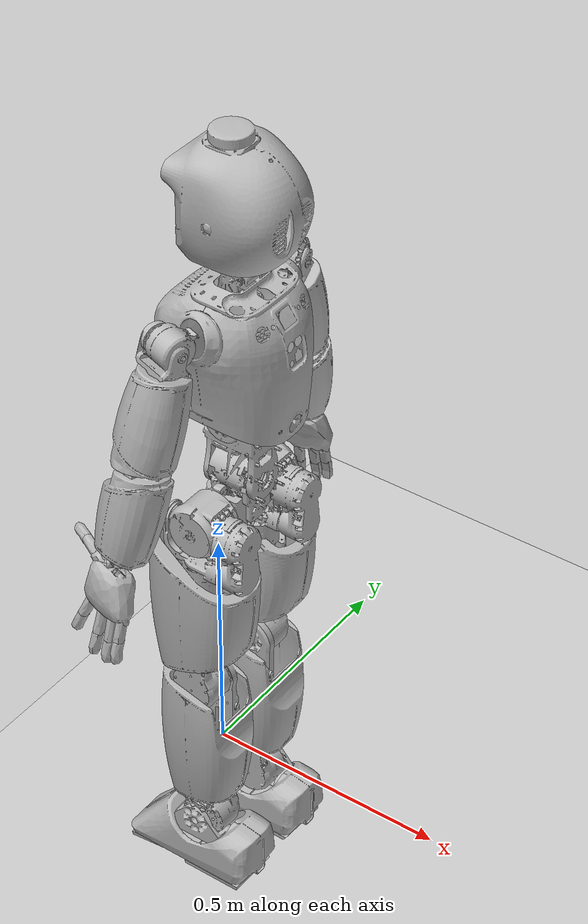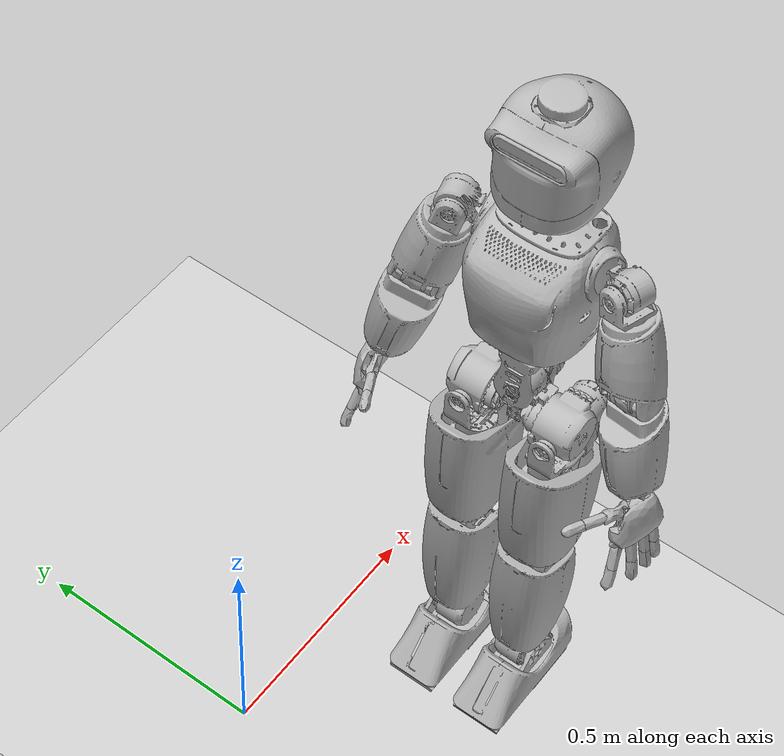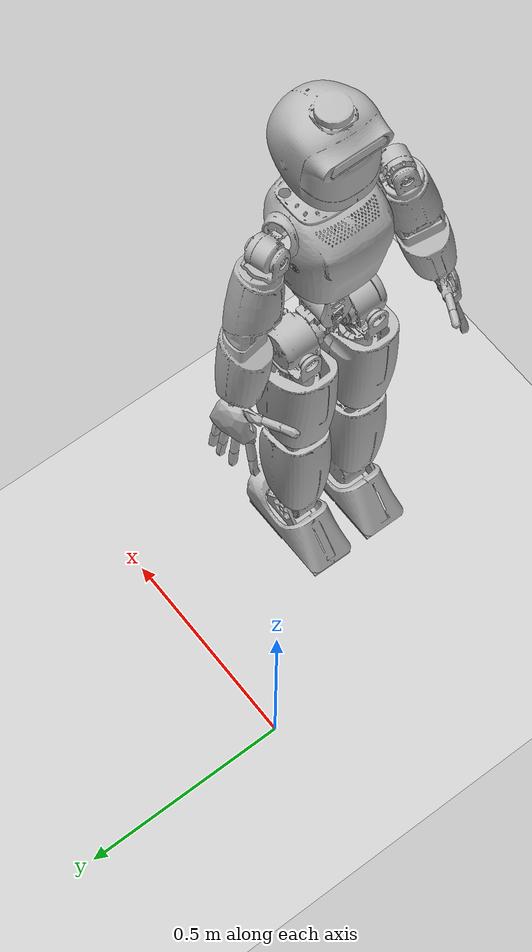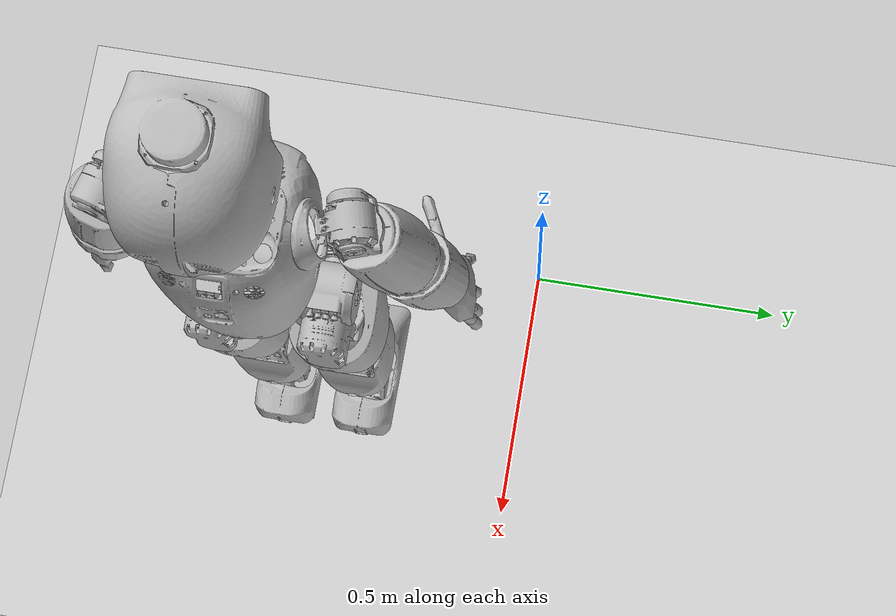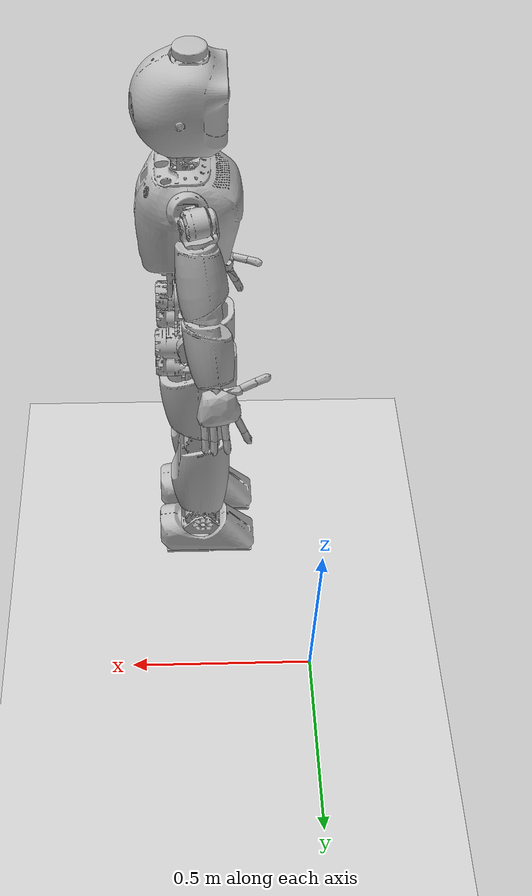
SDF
<sdf version="1.7">
 <world name="default">
  <light name="sun" type="directional">
   <pose>0 0 10 0 -0 0</pose>
   <diffuse>0.8 0.8 0.8 1</diffuse>
   <specular>0.2 0.2 0.2 1</specular>
   <attenuation>
    <range>1000</range>
    <constant>0.9</constant>
    <linear>0.01</linear>
    <quadratic>0.001</quadratic>
   </attenuation>
   <direction>-0.5 0.1 -0.9</direction>
   <spot><inner_angle>0</inner_angle><outer_angle>0</outer_angle><falloff>0</falloff></spot>
  </light>
  <model name="ground_plane">
   <static>1</static>
   <link name="link">
    <collision name="collision">
     <geometry><plane><normal>0 0 1</normal><size>100 100</size></plane></geometry>
     <surface>
      <contact><collide_bitmask>65535</collide_bitmask></contact>
      <friction><ode><mu>100</mu><mu2>50</mu2></ode></friction>
     </surface>
    </collision>
    <visual name="visual">
     <cast_shadows>0</cast_shadows>
     <geometry><plane><normal>0 0 1</normal><size>100 100</size></plane></geometry>
     <material>
      <script><uri>file://media/materials/scripts/gazebo.material</uri><name>Gazebo/Grey</name></script>
     </material>
    </visual>
   </link>
  </model>
  <gravity>0 0 -9.8</gravity>
  <magnetic_field>6e-06 2.3e-05 -4.2e-05</magnetic_field>
  <atmosphere type="adiabatic"/>
  <physics type="ode">
   <max_step_size>0.001</max_step_size>
   <real_time_factor>1</real_time_factor>
   <real_time_update_rate>1000</real_time_update_rate>
  </physics>
  <scene><ambient>0.4 0.4 0.4 1</ambient><background>0.7 0.7 0.7 1</background><shadows>1</shadows></scene>
  <spherical_coordinates>
   <surface_model>EARTH_WGS84</surface_model>
   <latitude_deg>0</latitude_deg>
   <longitude_deg>0</longitude_deg>
   <elevation>0</elevation>
   <heading_deg>0</heading_deg>
  </spherical_coordinates>
  <model name="ergocub_fixed">
   <frame name="ergoCub::__model__" attached_to="ergoCub::root_link">
    <pose relative_to="__model__">0 0 1 0 -0 3.14</pose>
   </frame>
   <link name="ergoCub::root_link">
    <inertial>
     <pose>0.002475 -0.000105 0.02345 0 -0 0</pose>
     <mass>2.82375</mass>
     <inertia>
      <ixx>0.00563061</ixx>
      <ixy>1.4369e-06</ixy>
      <ixz>2.32993e-05</ixz>
      <iyy>0.00438003</iyy>
      <iyz>1.40984e-05</iyz>
      <izz>0.00361668</izz>
     </inertia>
    </inertial>
    <collision name="root_link_collision">
     <geometry>
      <mesh>
       <scale>0.001 0.001 0.001</scale>
       <uri>model://ergoCub/meshes/simmechanics/sim_ecub_1-1_root_link.obj</uri>
      </mesh>
     </geometry>
    </collision>
    <visual name="root_link_visual">
     <geometry>
      <mesh>
       <scale>0.001 0.001 0.001</scale>
       <uri>model://ergoCub/meshes/simmechanics/sim_ecub_1-1_root_link.obj</uri>
      </mesh>
     </geometry>
    </visual>
    <pose relative_to="ergoCub::__model__">0 0 0 0 -0 0</pose>
   </link>
   <joint name="ergoCub::l_hip_pitch" type="revolute">
    <pose relative_to="ergoCub::root_link">0.0211 0.0505 0 0 -0 0</pose>
    <parent>ergoCub::root_link</parent>
    <child>ergoCub::l_hip_1</child>
    <axis>
     <xyz>-0 -1 -0</xyz>
     <limit><lower>-0.767945</lower><upper>1.91986</upper><effort>1e+09</effort><velocity>1e+09</velocity></limit>
     <dynamics>
      <damping>2</damping>
      <friction>0</friction>
      <spring_reference>0</spring_reference>
      <spring_stiffness>0</spring_stiffness>
     </dynamics>
    </axis>
    <physics>
     <ode>
      <implicit_spring_damper>1</implicit_spring_damper>
      <cfm_damping>1</cfm_damping>
      <limit><cfm>0</cfm><erp>0.2</erp></limit>
     </ode>
    </physics>
   </joint>
   <link name="ergoCub::l_hip_1">
    <pose relative_to="ergoCub::l_hip_pitch">0 0 0 0 -0 0</pose>
    <inertial>
     <pose>-0.004015 0.028247 -0.000681 0 -0 0</pose>
     <mass>2.23177</mass>
     <inertia>
      <ixx>0.00221092</ixx>
      <ixy>5.97126e-05</ixy>
      <ixz>-1.54322e-05</ixz>
      <iyy>0.00269533</iyy>
      <iyz>-5.83854e-06</iyz>
      <izz>0.00246104</izz>
     </inertia>
    </inertial>
    <collision name="l_hip_1_collision">
     <geometry>
      <mesh>
       <scale>0.001 0.001 0.001</scale>
       <uri>model://ergoCub/meshes/simmechanics/sim_ecub_1-1_l_hip_1.obj</uri>
      </mesh>
     </geometry>
    </collision>
    <visual name="l_hip_1_visual">
     <geometry>
      <mesh>
       <scale>0.001 0.001 0.001</scale>
       <uri>model://ergoCub/meshes/simmechanics/sim_ecub_1-1_l_hip_1.obj</uri>
      </mesh>
     </geometry>
    </visual>
   </link>
   <joint name="ergoCub::l_hip_roll" type="revolute">
    <pose relative_to="ergoCub::l_hip_1">-0.04725 0.0331 -0.009 0 -0 0</pose>
    <parent>ergoCub::l_hip_1</parent>
    <child>ergoCub::l_hip_2</child>
    <axis>
     <xyz>1 -0 0</xyz>
     <limit><lower>-0.349066</lower><upper>1.93732</upper><effort>1e+09</effort><velocity>1e+09</velocity></limit>
     <dynamics>
      <damping>2</damping>
      <friction>0</friction>
      <spring_reference>0</spring_reference>
      <spring_stiffness>0</spring_stiffness>
     </dynamics>
    </axis>
    <physics>
     <ode>
      <implicit_spring_damper>1</implicit_spring_damper>
      <cfm_damping>1</cfm_damping>
      <limit><cfm>0</cfm><erp>0.2</erp></limit>
     </ode>
    </physics>
   </joint>
   <link name="ergoCub::l_hip_2">
    <pose relative_to="ergoCub::l_hip_roll">0 0 0 0 -0 0</pose>
    <inertial>
     <pose>-0.004126 3.9e-05 -0.03751 0 -0 0</pose>
     <mass>1.83384</mass>
     <inertia>
      <ixx>0.00315951</ixx>
      <ixy>-1.65428e-06</ixy>
      <ixz>0.000997737</ixz>
      <iyy>0.00548824</iyy>
      <iyz>-2.19041e-06</iyz>
      <izz>0.00339849</izz>
     </inertia>
    </inertial>
    <collision name="l_hip_2_collision">
     <geometry>
      <mesh>
       <scale>0.001 0.001 0.001</scale>
       <uri>model://ergoCub/meshes/simmechanics/sim_ecub_1-1_l_hip_2.obj</uri>
      </mesh>
     </geometry>
    </collision>
    <visual name="l_hip_2_visual">
     <geometry>
      <mesh>
       <scale>0.001 0.001 0.001</scale>
       <uri>model://ergoCub/meshes/simmechanics/sim_ecub_1-1_l_hip_2.obj</uri>
      </mesh>
     </geometry>
    </visual>
   </link>
   <joint name="ergoCub::l_leg_ft_sensor" type="fixed">
    <pose relative_to="ergoCub::l_hip_2">0.0367 -0 -0.0897 0 -0 0</pose>
    <parent>ergoCub::l_hip_2</parent>
    <child>ergoCub::l_hip_3</child>
    <axis>
     <dynamics><spring_reference>0</spring_reference><spring_stiffness>0</spring_stiffness></dynamics>
     <xyz>0 0 1</xyz>
     <limit><lower>-1e+16</lower><upper>1e+16</upper></limit>
    </axis>
    <physics><ode><limit><cfm>0</cfm><erp>0.2</erp></limit></ode></physics>
    <sensor name="l_leg_ft" type="force_torque">
     <always_on>1</always_on>
     <update_rate>100</update_rate>
     <force_torque><frame>sensor</frame><measure_direction>child_to_parent</measure_direction></force_torque>
     <pose>0 0 0 3.14159 -0 2.61799</pose>
     <plugin name="left_leg_ft_plugin" filename="libgazebo_yarp_forcetorque.so">
      <yarpConfigurationFile>model://ergoCub/conf/FT/gazebo_ergocub_left_leg_ft.ini</yarpConfigurationFile>
     </plugin>
    </sensor>
   </joint>
   <link name="ergoCub::l_hip_3">
    <pose relative_to="ergoCub::l_leg_ft_sensor">0 0 0 0 -0 0</pose>
    <inertial>
     <pose>0.005176 -0.012829 -0.051749 0 -0 0</pose>
     <mass>2.14752</mass>
     <inertia>
      <ixx>0.00724216</ixx>
      <ixy>-3.32139e-05</ixy>
      <ixz>2.50599e-05</ixz>
      <iyy>0.00819796</iyy>
      <iyz>0.000124749</iyz>
      <izz>0.00572746</izz>
     </inertia>
    </inertial>
    <collision name="l_hip_3_collision">
     <geometry>
      <mesh>
       <scale>0.001 0.001 0.001</scale>
       <uri>model://ergoCub/meshes/simmechanics/sim_ecub_1-1_l_hip_3.obj</uri>
      </mesh>
     </geometry>
    </collision>
    <visual name="l_hip_3_visual">
     <geometry>
      <mesh>
       <scale>0.001 0.001 0.001</scale>
       <uri>model://ergoCub/meshes/simmechanics/sim_ecub_1-1_l_hip_3.obj</uri>
      </mesh>
     </geometry>
    </visual>
    <sensor name="l_leg_ft_imu" type="imu">
     <always_on>1</always_on>
     <update_rate>100</update_rate>
     <pose>0 0 0 3.14159 -0 2.61799</pose>
     <plugin name="ergocub_yarp_gazebo_plugin_IMU" filename="libgazebo_yarp_imu.so">
      <yarpConfigurationFile>model://ergoCub/conf/gazebo_ergocub_l_leg_ft_sensor_inertial.ini</yarpConfigurationFile>
     </plugin>
    </sensor>
   </link>
   <joint name="ergoCub::l_hip_yaw" type="revolute">
    <pose relative_to="ergoCub::l_hip_3">-0 -0.015 -0.0727 0 -0 0</pose>
    <parent>ergoCub::l_hip_3</parent>
    <child>ergoCub::l_upper_leg</child>
    <axis>
     <xyz>-0 0 1</xyz>
     <limit><lower>-1.41372</lower><upper>1.41372</upper><effort>1e+09</effort><velocity>1e+09</velocity></limit>
     <dynamics>
      <damping>2</damping>
      <friction>0</friction>
      <spring_reference>0</spring_reference>
      <spring_stiffness>0</spring_stiffness>
     </dynamics>
    </axis>
    <physics>
     <ode>
      <implicit_spring_damper>1</implicit_spring_damper>
      <cfm_damping>1</cfm_damping>
      <limit><cfm>0</cfm><erp>0.2</erp></limit>
     </ode>
    </physics>
   </joint>
   <link name="ergoCub::l_upper_leg">
    <pose relative_to="ergoCub::l_hip_yaw">0 0 0 0 -0 0</pose>
    <inertial>
     <pose>0.008503 0.014485 -0.126747 0 -0 0</pose>
     <mass>2.78492</mass>
     <inertia>
      <ixx>0.0118523</ixx>
      <ixy>-4.90715e-05</ixy>
      <ixz>0.000539393</ixz>
      <iyy>0.0121098</iyy>
      <iyz>0.000392089</iyz>
      <izz>0.00225363</izz>
     </inertia>
    </inertial>
    <collision name="l_upper_leg_collision">
     <geometry>
      <mesh>
       <scale>0.001 0.001 0.001</scale>
       <uri>model://ergoCub/meshes/simmechanics/sim_ecub_1-1_l_upper_leg.obj</uri>
      </mesh>
     </geometry>
    </collision>
    <visual name="l_upper_leg_visual">
     <geometry>
      <mesh>
       <scale>0.001 0.001 0.001</scale>
       <uri>model://ergoCub/meshes/simmechanics/sim_ecub_1-1_l_upper_leg.obj</uri>
      </mesh>
     </geometry>
    </visual>
   </link>
   <joint name="ergoCub::l_knee" type="revolute">
    <pose relative_to="ergoCub::l_upper_leg">0.0106 -0.0079 -0.1797 0 -0 0</pose>
    <parent>ergoCub::l_upper_leg</parent>
    <child>ergoCub::l_lower_leg</child>
    <axis>
     <xyz>-0 -1 0</xyz>
     <limit><lower>-1.8326</lower><upper>0.122173</upper><effort>1e+09</effort><velocity>1e+09</velocity></limit>
     <dynamics>
      <damping>2</damping>
      <friction>0</friction>
      <spring_reference>0</spring_reference>
      <spring_stiffness>0</spring_stiffness>
     </dynamics>
    </axis>
    <physics>
     <ode>
      <implicit_spring_damper>1</implicit_spring_damper>
      <cfm_damping>1</cfm_damping>
      <limit><cfm>0</cfm><erp>0.2</erp></limit>
     </ode>
    </physics>
   </joint>
   <link name="ergoCub::l_lower_leg">
    <pose relative_to="ergoCub::l_knee">0 0 0 0 -0 0</pose>
    <inertial>
     <pose>0.00142 0.006186 -0.213833 0 -0 0</pose>
     <mass>3.76758</mass>
     <inertia>
      <ixx>0.0464711</ixx>
      <ixy>-2.11893e-05</ixy>
      <ixz>-0.000811071</ixz>
      <iyy>0.0477673</iyy>
      <iyz>0.00181238</iyz>
      <izz>0.00484049</izz>
     </inertia>
    </inertial>
    <collision name="l_lower_leg_collision">
     <geometry>
      <mesh>
       <scale>0.001 0.001 0.001</scale>
       <uri>model://ergoCub/meshes/simmechanics/sim_ecub_1-1_l_lower_leg.obj</uri>
      </mesh>
     </geometry>
    </collision>
    <visual name="l_lower_leg_visual">
     <geometry>
      <mesh>
       <scale>0.001 0.001 0.001</scale>
       <uri>model://ergoCub/meshes/simmechanics/sim_ecub_1-1_l_lower_leg.obj</uri>
      </mesh>
     </geometry>
    </visual>
   </link>
   <joint name="ergoCub::l_ankle_pitch" type="revolute">
    <pose relative_to="ergoCub::l_lower_leg">-0 0.0319 -0.321 -0 -0 -0</pose>
    <parent>ergoCub::l_lower_leg</parent>
    <child>ergoCub::l_ankle_1</child>
    <axis>
     <xyz>-0 1 0</xyz>
     <limit><lower>-0.785398</lower><upper>0.785398</upper><effort>1e+09</effort><velocity>1e+09</velocity></limit>
     <dynamics>
      <damping>2</damping>
      <friction>0</friction>
      <spring_reference>0</spring_reference>
      <spring_stiffness>0</spring_stiffness>
     </dynamics>
    </axis>
    <physics>
     <ode>
      <implicit_spring_damper>1</implicit_spring_damper>
      <cfm_damping>1</cfm_damping>
      <limit><cfm>0</cfm><erp>0.2</erp></limit>
     </ode>
    </physics>
   </joint>
   <link name="ergoCub::l_ankle_1">
    <pose relative_to="ergoCub::l_ankle_pitch">0 0 0 0 -0 0</pose>
    <inertial>
     <pose>-0.001385 0.00066 -0.014087 0 -0 0</pose>
     <mass>0.348128</mass>
     <inertia><ixx>0.01</ixx><ixy>0</ixy><ixz>0</ixz><iyy>0.01</iyy><iyz>0</iyz><izz>0.01</izz></inertia>
    </inertial>
    <collision name="l_ankle_1_collision">
     <geometry>
      <mesh>
       <scale>0.001 0.001 0.001</scale>
       <uri>model://ergoCub/meshes/simmechanics/sim_ecub_1-1_l_ankle_1.obj</uri>
      </mesh>
     </geometry>
    </collision>
    <visual name="l_ankle_1_visual">
     <geometry>
      <mesh>
       <scale>0.001 0.001 0.001</scale>
       <uri>model://ergoCub/meshes/simmechanics/sim_ecub_1-1_l_ankle_1.obj</uri>
      </mesh>
     </geometry>
    </visual>
   </link>
   <joint name="ergoCub::l_ankle_roll" type="revolute">
    <pose relative_to="ergoCub::l_ankle_1">-0.05275 -0.0182 -0.035 0 -0 0</pose>
    <parent>ergoCub::l_ankle_1</parent>
    <child>ergoCub::l_ankle_2</child>
    <axis>
     <xyz>1 -0 -0</xyz>
     <limit><lower>-0.436332</lower><upper>0.436332</upper><effort>1e+09</effort><velocity>1e+09</velocity></limit>
     <dynamics>
      <damping>2</damping>
      <friction>0</friction>
      <spring_reference>0</spring_reference>
      <spring_stiffness>0</spring_stiffness>
     </dynamics>
    </axis>
    <physics>
     <ode>
      <implicit_spring_damper>1</implicit_spring_damper>
      <cfm_damping>1</cfm_damping>
      <limit><cfm>0</cfm><erp>0.2</erp></limit>
     </ode>
    </physics>
   </joint>
   <link name="ergoCub::l_ankle_2">
    <pose relative_to="ergoCub::l_ankle_roll">0 0 0 0 -0 0</pose>
    <inertial>
     <pose>0.040522 -9.8e-05 -0.023871 0 -0 0</pose>
     <mass>1.54182</mass>
     <inertia><ixx>0.01</ixx><ixy>0</ixy><ixz>0</ixz><iyy>0.01</iyy><iyz>0</iyz><izz>0.01</izz></inertia>
    </inertial>
    <collision name="l_ankle_2_collision">
     <geometry>
      <mesh>
       <scale>0.001 0.001 0.001</scale>
       <uri>model://ergoCub/meshes/simmechanics/sim_ecub_1-1_l_ankle_2.obj</uri>
      </mesh>
     </geometry>
    </collision>
    <visual name="l_ankle_2_visual">
     <geometry>
      <mesh>
       <scale>0.001 0.001 0.001</scale>
       <uri>model://ergoCub/meshes/simmechanics/sim_ecub_1-1_l_ankle_2.obj</uri>
      </mesh>
     </geometry>
    </visual>
   </link>
   <joint name="ergoCub::l_foot_front_ft_sensor" type="fixed">
    <pose relative_to="ergoCub::l_ankle_2">0.13525 -0 -0.0479 0 -0 0</pose>
    <parent>ergoCub::l_ankle_2</parent>
    <child>ergoCub::l_foot_front</child>
    <axis>
     <dynamics><spring_reference>0</spring_reference><spring_stiffness>0</spring_stiffness></dynamics>
     <xyz>0 0 1</xyz>
     <limit><lower>-1e+16</lower><upper>1e+16</upper></limit>
    </axis>
    <physics><ode><limit><cfm>0</cfm><erp>0.2</erp></limit></ode></physics>
    <sensor name="l_foot_front_ft" type="force_torque">
     <always_on>1</always_on>
     <update_rate>100</update_rate>
     <force_torque><frame>sensor</frame><measure_direction>parent_to_child</measure_direction></force_torque>
     <pose>0 0 0 0 0 -2.0944</pose>
     <plugin name="left_foot_front_ft_plugin" filename="libgazebo_yarp_forcetorque.so">
      <yarpConfigurationFile>model://ergoCub/conf/FT/gazebo_ergocub_left_foot_front_ft.ini</yarpConfigurationFile>
     </plugin>
    </sensor>
   </joint>
   <link name="ergoCub::l_foot_front">
    <pose relative_to="ergoCub::l_foot_front_ft_sensor">0 0 0 0 -0 0</pose>
    <inertial>
     <pose>0.000588 -0 -0.020001 0 -0 0</pose>
     <mass>0.221105</mass>
     <inertia><ixx>0.01</ixx><ixy>0</ixy><ixz>0</ixz><iyy>0.01</iyy><iyz>0</iyz><izz>0.01</izz></inertia>
    </inertial>
    <collision name="l_foot_front_collision">
     <pose>0 0 -0.0193 0 -0 0</pose>
     <geometry><box><size>0.117 0.1 0.006</size></box></geometry>
     <surface>
      <bounce><restitution_coefficient>0</restitution_coefficient><threshold>100000</threshold></bounce>
      <contact><ode><kp>1.8e+07</kp><kd>100</kd><max_vel>100</max_vel><min_depth>0.0001</min_depth></ode></contact>
      <friction><ode><mu>1</mu><mu2>1</mu2><fdir1>0 0 0</fdir1></ode></friction>
     </surface>
     <max_contacts>4</max_contacts>
    </collision>
    <visual name="l_foot_front_visual">
     <geometry>
      <mesh>
       <scale>0.001 0.001 0.001</scale>
       <uri>model://ergoCub/meshes/simmechanics/sim_ecub_1-1_l_foot_front.obj</uri>
      </mesh>
     </geometry>
    </visual>
    <sensor name="l_foot_front_ft_imu" type="imu">
     <always_on>1</always_on>
     <update_rate>100</update_rate>
     <pose>0 0 0 0 0 -2.0944</pose>
     <plugin name="ergocub_yarp_gazebo_plugin_IMU" filename="libgazebo_yarp_imu.so">
      <yarpConfigurationFile>model://ergoCub/conf/gazebo_ergocub_l_foot_front_ft_sensor_inertial.ini</yarpConfigurationFile>
     </plugin>
    </sensor>
   </link>
   <joint name="ergoCub::l_foot_rear_ft_sensor" type="fixed">
    <pose relative_to="ergoCub::l_ankle_2">0.016 -0 -0.0479 0 -0 0</pose>
    <parent>ergoCub::l_ankle_2</parent>
    <child>ergoCub::l_foot_rear</child>
    <axis>
     <dynamics><spring_reference>0</spring_reference><spring_stiffness>0</spring_stiffness></dynamics>
     <xyz>0 0 1</xyz>
     <limit><lower>-1e+16</lower><upper>1e+16</upper></limit>
    </axis>
    <physics><ode><limit><cfm>0</cfm><erp>0.2</erp></limit></ode></physics>
    <sensor name="l_foot_rear_ft" type="force_torque">
     <always_on>1</always_on>
     <update_rate>100</update_rate>
     <force_torque><frame>sensor</frame><measure_direction>parent_to_child</measure_direction></force_torque>
     <pose>0 0 0 0 0 -2.0944</pose>
     <plugin name="left_foot_rear_ft_plugin" filename="libgazebo_yarp_forcetorque.so">
      <yarpConfigurationFile>model://ergoCub/conf/FT/gazebo_ergocub_left_foot_rear_ft.ini</yarpConfigurationFile>
     </plugin>
    </sensor>
   </joint>
   <link name="ergoCub::l_foot_rear">
    <pose relative_to="ergoCub::l_foot_rear_ft_sensor">0 0 0 0 -0 0</pose>
    <inertial>
     <pose>0.000588 -0 -0.020001 0 -0 0</pose>
     <mass>0.221105</mass>
     <inertia><ixx>0.01</ixx><ixy>0</ixy><ixz>0</ixz><iyy>0.01</iyy><iyz>0</iyz><izz>0.01</izz></inertia>
    </inertial>
    <collision name="l_foot_rear_collision">
     <pose>0 0 -0.0193 0 -0 0</pose>
     <geometry><box><size>0.117 0.1 0.006</size></box></geometry>
     <surface>
      <bounce><restitution_coefficient>0</restitution_coefficient><threshold>100000</threshold></bounce>
      <contact><ode><kp>1.8e+07</kp><kd>100</kd><max_vel>100</max_vel><min_depth>0.0001</min_depth></ode></contact>
      <friction><ode><mu>1</mu><mu2>1</mu2><fdir1>0 0 0</fdir1></ode></friction>
     </surface>
     <max_contacts>4</max_contacts>
    </collision>
    <visual name="l_foot_rear_visual">
     <geometry>
      <mesh>
       <scale>0.001 0.001 0.001</scale>
       <uri>model://ergoCub/meshes/simmechanics/sim_ecub_1-1_l_foot_rear.obj</uri>
      </mesh>
     </geometry>
    </visual>
    <sensor name="l_foot_rear_ft_imu" type="imu">
     <always_on>1</always_on>
     <update_rate>100</update_rate>
     <pose>0 0 0 0 0 -2.0944</pose>
     <plugin name="ergocub_yarp_gazebo_plugin_IMU" filename="libgazebo_yarp_imu.so">
      <yarpConfigurationFile>model://ergoCub/conf/gazebo_ergocub_l_foot_rear_ft_sensor_inertial.ini</yarpConfigurationFile>
     </plugin>
    </sensor>
   </link>
   <joint name="ergoCub::r_hip_pitch" type="revolute">
    <pose relative_to="ergoCub::root_link">0.0211 -0.0505 -0 0 -0 0</pose>
    <parent>ergoCub::root_link</parent>
    <child>ergoCub::r_hip_1</child>
    <axis>
     <xyz>-0 -1 0</xyz>
     <limit><lower>-0.767945</lower><upper>1.91986</upper><effort>1e+09</effort><velocity>1e+09</velocity></limit>
     <dynamics>
      <damping>2</damping>
      <friction>0</friction>
      <spring_reference>0</spring_reference>
      <spring_stiffness>0</spring_stiffness>
     </dynamics>
    </axis>
    <physics>
     <ode>
      <implicit_spring_damper>1</implicit_spring_damper>
      <cfm_damping>1</cfm_damping>
      <limit><cfm>0</cfm><erp>0.2</erp></limit>
     </ode>
    </physics>
   </joint>
   <link name="ergoCub::r_hip_1">
    <pose relative_to="ergoCub::r_hip_pitch">0 0 0 0 -0 0</pose>
    <inertial>
     <pose>-0.004032 -0.028249 -0.000674 0 -0 0</pose>
     <mass>2.23209</mass>
     <inertia>
      <ixx>0.00221226</ixx>
      <ixy>-6.12672e-05</ixy>
      <ixz>-1.50357e-05</ixz>
      <iyy>0.00269555</iyy>
      <iyz>6.44336e-06</iyz>
      <izz>0.00246089</izz>
     </inertia>
    </inertial>
    <collision name="r_hip_1_collision">
     <geometry>
      <mesh>
       <scale>0.001 0.001 0.001</scale>
       <uri>model://ergoCub/meshes/simmechanics/sim_ecub_1-1_r_hip_1.obj</uri>
      </mesh>
     </geometry>
    </collision>
    <visual name="r_hip_1_visual">
     <geometry>
      <mesh>
       <scale>0.001 0.001 0.001</scale>
       <uri>model://ergoCub/meshes/simmechanics/sim_ecub_1-1_r_hip_1.obj</uri>
      </mesh>
     </geometry>
    </visual>
   </link>
   <joint name="ergoCub::r_hip_roll" type="revolute">
    <pose relative_to="ergoCub::r_hip_1">-0.04725 -0.0331 -0.009 0 -0 0</pose>
    <parent>ergoCub::r_hip_1</parent>
    <child>ergoCub::r_hip_2</child>
    <axis>
     <xyz>-1 -0 -0</xyz>
     <limit><lower>-0.349066</lower><upper>1.93732</upper><effort>1e+09</effort><velocity>1e+09</velocity></limit>
     <dynamics>
      <damping>2</damping>
      <friction>0</friction>
      <spring_reference>0</spring_reference>
      <spring_stiffness>0</spring_stiffness>
     </dynamics>
    </axis>
    <physics>
     <ode>
      <implicit_spring_damper>1</implicit_spring_damper>
      <cfm_damping>1</cfm_damping>
      <limit><cfm>0</cfm><erp>0.2</erp></limit>
     </ode>
    </physics>
   </joint>
   <link name="ergoCub::r_hip_2">
    <pose relative_to="ergoCub::r_hip_roll">0 0 0 0 -0 0</pose>
    <inertial>
     <pose>-0.004339 -4.3e-05 -0.037116 0 -0 0</pose>
     <mass>1.84254</mass>
     <inertia>
      <ixx>0.0031203</ixx>
      <ixy>2.37353e-06</ixy>
      <ixz>0.00101247</ixz>
      <iyy>0.00545917</iyy>
      <iyz>-1.8524e-06</iyz>
      <izz>0.003419</izz>
     </inertia>
    </inertial>
    <collision name="r_hip_2_collision">
     <geometry>
      <mesh>
       <scale>0.001 0.001 0.001</scale>
       <uri>model://ergoCub/meshes/simmechanics/sim_ecub_1-1_r_hip_2.obj</uri>
      </mesh>
     </geometry>
    </collision>
    <visual name="r_hip_2_visual">
     <geometry>
      <mesh>
       <scale>0.001 0.001 0.001</scale>
       <uri>model://ergoCub/meshes/simmechanics/sim_ecub_1-1_r_hip_2.obj</uri>
      </mesh>
     </geometry>
    </visual>
   </link>
   <joint name="ergoCub::r_leg_ft_sensor" type="fixed">
    <pose relative_to="ergoCub::r_hip_2">0.0367 -0 -0.0897 0 -0 0</pose>
    <parent>ergoCub::r_hip_2</parent>
    <child>ergoCub::r_hip_3</child>
    <axis>
     <dynamics><spring_reference>0</spring_reference><spring_stiffness>0</spring_stiffness></dynamics>
     <xyz>0 0 1</xyz>
     <limit><lower>-1e+16</lower><upper>1e+16</upper></limit>
    </axis>
    <physics><ode><limit><cfm>0</cfm><erp>0.2</erp></limit></ode></physics>
    <sensor name="r_leg_ft" type="force_torque">
     <always_on>1</always_on>
     <update_rate>100</update_rate>
     <force_torque><frame>sensor</frame><measure_direction>child_to_parent</measure_direction></force_torque>
     <pose>0 0 0 3.14159 -0 -2.61799</pose>
     <plugin name="right_leg_ft_plugin" filename="libgazebo_yarp_forcetorque.so">
      <yarpConfigurationFile>model://ergoCub/conf/FT/gazebo_ergocub_right_leg_ft.ini</yarpConfigurationFile>
     </plugin>
    </sensor>
   </joint>
   <link name="ergoCub::r_hip_3">
    <pose relative_to="ergoCub::r_leg_ft_sensor">0 0 0 0 -0 0</pose>
    <inertial>
     <pose>0.005151 0.012832 -0.051688 0 -0 0</pose>
     <mass>2.1479</mass>
     <inertia>
      <ixx>0.00719318</ixx>
      <ixy>3.49873e-05</ixy>
      <ixz>2.40967e-05</ixz>
      <iyy>0.008149</iyy>
      <iyz>-0.000125728</iyz>
      <izz>0.00572783</izz>
     </inertia>
    </inertial>
    <collision name="r_hip_3_collision">
     <geometry>
      <mesh>
       <scale>0.001 0.001 0.001</scale>
       <uri>model://ergoCub/meshes/simmechanics/sim_ecub_1-1_r_hip_3.obj</uri>
      </mesh>
     </geometry>
    </collision>
    <visual name="r_hip_3_visual">
     <geometry>
      <mesh>
       <scale>0.001 0.001 0.001</scale>
       <uri>model://ergoCub/meshes/simmechanics/sim_ecub_1-1_r_hip_3.obj</uri>
      </mesh>
     </geometry>
    </visual>
    <sensor name="r_leg_ft_imu" type="imu">
     <always_on>1</always_on>
     <update_rate>100</update_rate>
     <pose>0 0 0 3.14159 -0 -2.61799</pose>
     <plugin name="ergocub_yarp_gazebo_plugin_IMU" filename="libgazebo_yarp_imu.so">
      <yarpConfigurationFile>model://ergoCub/conf/gazebo_ergocub_r_leg_ft_sensor_inertial.ini</yarpConfigurationFile>
     </plugin>
    </sensor>
   </link>
   <joint name="ergoCub::r_hip_yaw" type="revolute">
    <pose relative_to="ergoCub::r_hip_3">-0 0.015 -0.0727 0 -0 1e-06</pose>
    <parent>ergoCub::r_hip_3</parent>
    <child>ergoCub::r_upper_leg</child>
    <axis>
     <xyz>-0 0 -1</xyz>
     <limit><lower>-1.41372</lower><upper>1.41372</upper><effort>1e+09</effort><velocity>1e+09</velocity></limit>
     <dynamics>
      <damping>2</damping>
      <friction>0</friction>
      <spring_reference>0</spring_reference>
      <spring_stiffness>0</spring_stiffness>
     </dynamics>
    </axis>
    <physics>
     <ode>
      <implicit_spring_damper>1</implicit_spring_damper>
      <cfm_damping>1</cfm_damping>
      <limit><cfm>0</cfm><erp>0.2</erp></limit>
     </ode>
    </physics>
   </joint>
   <link name="ergoCub::r_upper_leg">
    <pose relative_to="ergoCub::r_hip_yaw">0 0 0 0 -0 0</pose>
    <inertial>
     <pose>0.008517 -0.014468 -0.12675 0 -0 0</pose>
     <mass>2.78492</mass>
     <inertia>
      <ixx>0.0118601</ixx>
      <ixy>5.45545e-05</ixy>
      <ixz>0.000539357</ixz>
      <iyy>0.0121091</iyy>
      <iyz>-0.00040331</iyz>
      <izz>0.00226097</izz>
     </inertia>
    </inertial>
    <collision name="r_upper_leg_collision">
     <geometry>
      <mesh>
       <scale>0.001 0.001 0.001</scale>
       <uri>model://ergoCub/meshes/simmechanics/sim_ecub_1-1_r_upper_leg.obj</uri>
      </mesh>
     </geometry>
    </collision>
    <visual name="r_upper_leg_visual">
     <geometry>
      <mesh>
       <scale>0.001 0.001 0.001</scale>
       <uri>model://ergoCub/meshes/simmechanics/sim_ecub_1-1_r_upper_leg.obj</uri>
      </mesh>
     </geometry>
    </visual>
   </link>
   <joint name="ergoCub::r_knee" type="revolute">
    <pose relative_to="ergoCub::r_upper_leg">0.0106 0.0079 -0.1797 0 -0 -1e-06</pose>
    <parent>ergoCub::r_upper_leg</parent>
    <child>ergoCub::r_lower_leg</child>
    <axis>
     <xyz>1e-06 -1 0</xyz>
     <limit><lower>-1.8326</lower><upper>0.122173</upper><effort>1e+09</effort><velocity>1e+09</velocity></limit>
     <dynamics>
      <damping>2</damping>
      <friction>0</friction>
      <spring_reference>0</spring_reference>
      <spring_stiffness>0</spring_stiffness>
     </dynamics>
    </axis>
    <physics>
     <ode>
      <implicit_spring_damper>1</implicit_spring_damper>
      <cfm_damping>1</cfm_damping>
      <limit><cfm>0</cfm><erp>0.2</erp></limit>
     </ode>
    </physics>
   </joint>
   <link name="ergoCub::r_lower_leg">
    <pose relative_to="ergoCub::r_knee">0 0 0 0 -0 0</pose>
    <inertial>
     <pose>0.001216 -0.006185 -0.213728 0 -0 0</pose>
     <mass>3.76215</mass>
     <inertia>
      <ixx>0.0464422</ixx>
      <ixy>3.72693e-05</ixy>
      <ixz>-0.000851989</ixz>
      <iyy>0.0477389</iyy>
      <iyz>-0.0018043</iyz>
      <izz>0.00483967</izz>
     </inertia>
    </inertial>
    <collision name="r_lower_leg_collision">
     <geometry>
      <mesh>
       <scale>0.001 0.001 0.001</scale>
       <uri>model://ergoCub/meshes/simmechanics/sim_ecub_1-1_r_lower_leg.obj</uri>
      </mesh>
     </geometry>
    </collision>
    <visual name="r_lower_leg_visual">
     <geometry>
      <mesh>
       <scale>0.001 0.001 0.001</scale>
       <uri>model://ergoCub/meshes/simmechanics/sim_ecub_1-1_r_lower_leg.obj</uri>
      </mesh>
     </geometry>
    </visual>
   </link>
   <joint name="ergoCub::r_ankle_pitch" type="revolute">
    <pose relative_to="ergoCub::r_lower_leg">-0 -0.0319 -0.321 0 -0 0</pose>
    <parent>ergoCub::r_lower_leg</parent>
    <child>ergoCub::r_ankle_1</child>
    <axis>
     <xyz>-0 1 -0</xyz>
     <limit><lower>-0.785398</lower><upper>0.785398</upper><effort>1e+09</effort><velocity>1e+09</velocity></limit>
     <dynamics>
      <damping>2</damping>
      <friction>0</friction>
      <spring_reference>0</spring_reference>
      <spring_stiffness>0</spring_stiffness>
     </dynamics>
    </axis>
    <physics>
     <ode>
      <implicit_spring_damper>1</implicit_spring_damper>
      <cfm_damping>1</cfm_damping>
      <limit><cfm>0</cfm><erp>0.2</erp></limit>
     </ode>
    </physics>
   </joint>
   <link name="ergoCub::r_ankle_1">
    <pose relative_to="ergoCub::r_ankle_pitch">0 0 0 0 -0 0</pose>
    <inertial>
     <pose>-0.001367 -0.00066 -0.014087 0 -0 0</pose>
     <mass>0.348128</mass>
     <inertia><ixx>0.01</ixx><ixy>0</ixy><ixz>0</ixz><iyy>0.01</iyy><iyz>0</iyz><izz>0.01</izz></inertia>
    </inertial>
    <collision name="r_ankle_1_collision">
     <geometry>
      <mesh>
       <scale>0.001 0.001 0.001</scale>
       <uri>model://ergoCub/meshes/simmechanics/sim_ecub_1-1_r_ankle_1.obj</uri>
      </mesh>
     </geometry>
    </collision>
    <visual name="r_ankle_1_visual">
     <geometry>
      <mesh>
       <scale>0.001 0.001 0.001</scale>
       <uri>model://ergoCub/meshes/simmechanics/sim_ecub_1-1_r_ankle_1.obj</uri>
      </mesh>
     </geometry>
    </visual>
   </link>
   <joint name="ergoCub::r_ankle_roll" type="revolute">
    <pose relative_to="ergoCub::r_ankle_1">-0.05275 0.0182 -0.035 0 -0 0</pose>
    <parent>ergoCub::r_ankle_1</parent>
    <child>ergoCub::r_ankle_2</child>
    <axis>
     <xyz>-1 -0 0</xyz>
     <limit><lower>-0.436332</lower><upper>0.436332</upper><effort>1e+09</effort><velocity>1e+09</velocity></limit>
     <dynamics>
      <damping>2</damping>
      <friction>0</friction>
      <spring_reference>0</spring_reference>
      <spring_stiffness>0</spring_stiffness>
     </dynamics>
    </axis>
    <physics>
     <ode>
      <implicit_spring_damper>1</implicit_spring_damper>
      <cfm_damping>1</cfm_damping>
      <limit><cfm>0</cfm><erp>0.2</erp></limit>
     </ode>
    </physics>
   </joint>
   <link name="ergoCub::r_ankle_2">
    <pose relative_to="ergoCub::r_ankle_roll">0 0 0 0 -0 0</pose>
    <inertial>
     <pose>0.040526 -8.6e-05 -0.023871 0 -0 0</pose>
     <mass>1.54182</mass>
     <inertia><ixx>0.01</ixx><ixy>0</ixy><ixz>0</ixz><iyy>0.01</iyy><iyz>0</iyz><izz>0.01</izz></inertia>
    </inertial>
    <collision name="r_ankle_2_collision">
     <geometry>
      <mesh>
       <scale>0.001 0.001 0.001</scale>
       <uri>model://ergoCub/meshes/simmechanics/sim_ecub_1-1_r_ankle_2.obj</uri>
      </mesh>
     </geometry>
    </collision>
    <visual name="r_ankle_2_visual">
     <geometry>
      <mesh>
       <scale>0.001 0.001 0.001</scale>
       <uri>model://ergoCub/meshes/simmechanics/sim_ecub_1-1_r_ankle_2.obj</uri>
      </mesh>
     </geometry>
    </visual>
   </link>
   <joint name="ergoCub::r_foot_front_ft_sensor" type="fixed">
    <pose relative_to="ergoCub::r_ankle_2">0.13525 0 -0.0479 0 -0 0</pose>
    <parent>ergoCub::r_ankle_2</parent>
    <child>ergoCub::r_foot_front</child>
    <axis>
     <dynamics><spring_reference>0</spring_reference><spring_stiffness>0</spring_stiffness></dynamics>
     <xyz>0 0 1</xyz>
     <limit><lower>-1e+16</lower><upper>1e+16</upper></limit>
    </axis>
    <physics><ode><limit><cfm>0</cfm><erp>0.2</erp></limit></ode></physics>
    <sensor name="r_foot_front_ft" type="force_torque">
     <always_on>1</always_on>
     <update_rate>100</update_rate>
     <force_torque><frame>sensor</frame><measure_direction>parent_to_child</measure_direction></force_torque>
     <pose>0 0 0 -0 -0 -2.0944</pose>
     <plugin name="right_foot_front_ft_plugin" filename="libgazebo_yarp_forcetorque.so">
      <yarpConfigurationFile>model://ergoCub/conf/FT/gazebo_ergocub_right_foot_front_ft.ini</yarpConfigurationFile>
     </plugin>
    </sensor>
   </joint>
   <link name="ergoCub::r_foot_front">
    <pose relative_to="ergoCub::r_foot_front_ft_sensor">0 0 0 0 -0 0</pose>
    <inertial>
     <pose>0.000588 -0 -0.020001 0 -0 0</pose>
     <mass>0.221105</mass>
     <inertia><ixx>0.01</ixx><ixy>0</ixy><ixz>0</ixz><iyy>0.01</iyy><iyz>0</iyz><izz>0.01</izz></inertia>
    </inertial>
    <collision name="r_foot_front_collision">
     <pose>0 0 -0.0193 0 -0 0</pose>
     <geometry><box><size>0.117 0.1 0.006</size></box></geometry>
     <surface>
      <bounce><restitution_coefficient>0</restitution_coefficient><threshold>100000</threshold></bounce>
      <contact><ode><kp>1.8e+07</kp><kd>100</kd><max_vel>100</max_vel><min_depth>0.0001</min_depth></ode></contact>
      <friction><ode><mu>1</mu><mu2>1</mu2><fdir1>0 0 0</fdir1></ode></friction>
     </surface>
     <max_contacts>4</max_contacts>
    </collision>
    <visual name="r_foot_front_visual">
     <geometry>
      <mesh>
       <scale>0.001 0.001 0.001</scale>
       <uri>model://ergoCub/meshes/simmechanics/sim_ecub_1-1_r_foot_front.obj</uri>
      </mesh>
     </geometry>
    </visual>
    <sensor name="r_foot_front_ft_imu" type="imu">
     <always_on>1</always_on>
     <update_rate>100</update_rate>
     <pose>0 0 0 -0 -0 -2.0944</pose>
     <plugin name="ergocub_yarp_gazebo_plugin_IMU" filename="libgazebo_yarp_imu.so">
      <yarpConfigurationFile>model://ergoCub/conf/gazebo_ergocub_r_foot_front_ft_sensor_inertial.ini</yarpConfigurationFile>
     </plugin>
    </sensor>
   </link>
   <joint name="ergoCub::r_foot_rear_ft_sensor" type="fixed">
    <pose relative_to="ergoCub::r_ankle_2">0.016 0 -0.0479 0 -0 0</pose>
    <parent>ergoCub::r_ankle_2</parent>
    <child>ergoCub::r_foot_rear</child>
    <axis>
     <dynamics><spring_reference>0</spring_reference><spring_stiffness>0</spring_stiffness></dynamics>
     <xyz>0 0 1</xyz>
     <limit><lower>-1e+16</lower><upper>1e+16</upper></limit>
    </axis>
    <physics><ode><limit><cfm>0</cfm><erp>0.2</erp></limit></ode></physics>
    <sensor name="r_foot_rear_ft" type="force_torque">
     <always_on>1</always_on>
     <update_rate>100</update_rate>
     <force_torque><frame>sensor</frame><measure_direction>parent_to_child</measure_direction></force_torque>
     <pose>0 0 0 -0 -0 -2.0944</pose>
     <plugin name="right_foot_rear_ft_plugin" filename="libgazebo_yarp_forcetorque.so">
      <yarpConfigurationFile>model://ergoCub/conf/FT/gazebo_ergocub_right_foot_rear_ft.ini</yarpConfigurationFile>
     </plugin>
    </sensor>
   </joint>
   <link name="ergoCub::r_foot_rear">
    <pose relative_to="ergoCub::r_foot_rear_ft_sensor">0 0 0 0 -0 0</pose>
    <inertial>
     <pose>0.000588 -0 -0.020001 0 -0 0</pose>
     <mass>0.221105</mass>
     <inertia><ixx>0.01</ixx><ixy>0</ixy><ixz>0</ixz><iyy>0.01</iyy><iyz>0</iyz><izz>0.01</izz></inertia>
    </inertial>
    <collision name="r_foot_rear_collision">
     <pose>0 0 -0.0193 0 -0 0</pose>
     <geometry><box><size>0.117 0.1 0.006</size></box></geometry>
     <surface>
      <bounce><restitution_coefficient>0</restitution_coefficient><threshold>100000</threshold></bounce>
      <contact><ode><kp>1.8e+07</kp><kd>100</kd><max_vel>100</max_vel><min_depth>0.0001</min_depth></ode></contact>
      <friction><ode><mu>1</mu><mu2>1</mu2><fdir1>0 0 0</fdir1></ode></friction>
     </surface>
     <max_contacts>4</max_contacts>
    </collision>
    <visual name="r_foot_rear_visual">
     <geometry>
      <mesh>
       <scale>0.001 0.001 0.001</scale>
       <uri>model://ergoCub/meshes/simmechanics/sim_ecub_1-1_r_foot_rear.obj</uri>
      </mesh>
     </geometry>
    </visual>
    <sensor name="r_foot_rear_ft_imu" type="imu">
     <always_on>1</always_on>
     <update_rate>100</update_rate>
     <pose>0 0 0 -0 -0 -2.0944</pose>
     <plugin name="ergocub_yarp_gazebo_plugin_IMU" filename="libgazebo_yarp_imu.so">
      <yarpConfigurationFile>model://ergoCub/conf/gazebo_ergocub_r_foot_rear_ft_sensor_inertial.ini</yarpConfigurationFile>
     </plugin>
    </sensor>
   </link>
   <joint name="ergoCub::torso_roll" type="revolute">
    <pose relative_to="ergoCub::root_link">-0 -0 0.0605 0 -0 0</pose>
    <parent>ergoCub::root_link</parent>
    <child>ergoCub::torso_1</child>
    <axis>
     <xyz>-1 0 0</xyz>
     <limit><lower>-0.436332</lower><upper>0.436332</upper><effort>1e+09</effort><velocity>1e+09</velocity></limit>
     <dynamics>
      <damping>2</damping>
      <friction>0</friction>
      <spring_reference>0</spring_reference>
      <spring_stiffness>0</spring_stiffness>
     </dynamics>
    </axis>
    <physics>
     <ode>
      <implicit_spring_damper>1</implicit_spring_damper>
      <cfm_damping>1</cfm_damping>
      <limit><cfm>0</cfm><erp>0.2</erp></limit>
     </ode>
    </physics>
   </joint>
   <link name="ergoCub::torso_1">
    <pose relative_to="ergoCub::torso_roll">0 0 0 0 -0 0</pose>
    <inertial>
     <pose>-0.00964 0.000617 0.082442 0 -0 0</pose>
     <mass>2.06457</mass>
     <inertia>
      <ixx>0.00740609</ixx>
      <ixy>0</ixy>
      <ixz>0</ixz>
      <iyy>0.00594707</iyy>
      <iyz>0</iyz>
      <izz>0.00317801</izz>
     </inertia>
    </inertial>
    <collision name="torso_1_collision">
     <geometry>
      <mesh>
       <scale>0.001 0.001 0.001</scale>
       <uri>model://ergoCub/meshes/simmechanics/sim_ecub_1-1_torso_1.obj</uri>
      </mesh>
     </geometry>
    </collision>
    <visual name="torso_1_visual">
     <geometry>
      <mesh>
       <scale>0.001 0.001 0.001</scale>
       <uri>model://ergoCub/meshes/simmechanics/sim_ecub_1-1_torso_1.obj</uri>
      </mesh>
     </geometry>
    </visual>
    <sensor name="waist_imu_0" type="imu">
     <always_on>1</always_on>
     <update_rate>100</update_rate>
     <pose>0.0606 -0.006394 0.01745 1.5708 -0.000105 -1.5708</pose>
     <plugin name="ergocub_yarp_gazebo_plugin_IMU" filename="libgazebo_yarp_imu.so">
      <yarpConfigurationFile>model://ergoCub/conf/gazebo_ergocub_waist_inertial.ini</yarpConfigurationFile>
     </plugin>
    </sensor>
   </link>
   <joint name="ergoCub::torso_pitch" type="revolute">
    <pose relative_to="ergoCub::torso_1">-0 -0 0.118 0 -0 0</pose>
    <parent>ergoCub::torso_1</parent>
    <child>ergoCub::torso_2</child>
    <axis>
     <xyz>0 1 0</xyz>
     <limit><lower>-0.349066</lower><upper>1.13446</upper><effort>1e+09</effort><velocity>1e+09</velocity></limit>
     <dynamics>
      <damping>2</damping>
      <friction>0</friction>
      <spring_reference>0</spring_reference>
      <spring_stiffness>0</spring_stiffness>
     </dynamics>
    </axis>
    <physics>
     <ode>
      <implicit_spring_damper>1</implicit_spring_damper>
      <cfm_damping>1</cfm_damping>
      <limit><cfm>0</cfm><erp>0.2</erp></limit>
     </ode>
    </physics>
   </joint>
   <link name="ergoCub::torso_2">
    <pose relative_to="ergoCub::torso_pitch">0 0 0 0 -0 0</pose>
    <inertial>
     <pose>0.001572 0.003622 0.02602 0 -0 0</pose>
     <mass>0.705163</mass>
     <inertia>
      <ixx>0.00125903</ixx>
      <ixy>4.19862e-06</ixy>
      <ixz>-5.39816e-06</ixz>
      <iyy>0.000667553</iyy>
      <iyz>7.0143e-05</iyz>
      <izz>0.00114582</izz>
     </inertia>
    </inertial>
    <collision name="torso_2_collision">
     <geometry>
      <mesh>
       <scale>0.001 0.001 0.001</scale>
       <uri>model://ergoCub/meshes/simmechanics/sim_ecub_1-1_torso_2.obj</uri>
      </mesh>
     </geometry>
    </collision>
    <visual name="torso_2_visual">
     <geometry>
      <mesh>
       <scale>0.001 0.001 0.001</scale>
       <uri>model://ergoCub/meshes/simmechanics/sim_ecub_1-1_torso_2.obj</uri>
      </mesh>
     </geometry>
    </visual>
   </link>
   <joint name="ergoCub::torso_yaw" type="revolute">
    <pose relative_to="ergoCub::torso_2">0 0 0.06447 -0 -0 -0</pose>
    <parent>ergoCub::torso_2</parent>
    <child>ergoCub::chest</child>
    <axis>
     <xyz>0 -0 -1</xyz>
     <limit><lower>-0.785398</lower><upper>0.785398</upper><effort>1e+09</effort><velocity>1e+09</velocity></limit>
     <dynamics>
      <damping>2</damping>
      <friction>0</friction>
      <spring_reference>0</spring_reference>
      <spring_stiffness>0</spring_stiffness>
     </dynamics>
    </axis>
    <physics>
     <ode>
      <implicit_spring_damper>1</implicit_spring_damper>
      <cfm_damping>1</cfm_damping>
      <limit><cfm>0</cfm><erp>0.2</erp></limit>
     </ode>
    </physics>
   </joint>
   <link name="ergoCub::chest">
    <pose relative_to="ergoCub::torso_yaw">0 0 0 0 -0 0</pose>
    <inertial>
     <pose>-0.010721 -0.000348 0.076111 0 -0 0</pose>
     <mass>8.06547</mass>
     <inertia>
      <ixx>0.0484548</ixx>
      <ixy>0.000176119</ixy>
      <ixz>-0.000312409</ixz>
      <iyy>0.0449388</iyy>
      <iyz>-0.00012962</iyz>
      <izz>0.0306877</izz>
     </inertia>
    </inertial>
    <collision name="chest_collision">
     <geometry>
      <mesh>
       <scale>0.001 0.001 0.001</scale>
       <uri>model://ergoCub/meshes/simmechanics/sim_ecub_1-1_chest.obj</uri>
      </mesh>
     </geometry>
    </collision>
    <visual name="chest_visual">
     <geometry>
      <mesh>
       <scale>0.001 0.001 0.001</scale>
       <uri>model://ergoCub/meshes/simmechanics/sim_ecub_1-1_chest.obj</uri>
      </mesh>
     </geometry>
    </visual>
   </link>
   <joint name="ergoCub::l_shoulder_pitch" type="revolute">
    <pose relative_to="ergoCub::chest">-0.013519 0.067048 0.12352 0.253612 -0.052032 -0.275279</pose>
    <parent>ergoCub::chest</parent>
    <child>ergoCub::l_shoulder_1</child>
    <axis>
     <xyz>-0 1 0</xyz>
     <limit><lower>-2.96706</lower><upper>0.610865</upper><effort>1e+09</effort><velocity>1e+09</velocity></limit>
     <dynamics>
      <damping>2</damping>
      <friction>0</friction>
      <spring_reference>0</spring_reference>
      <spring_stiffness>0</spring_stiffness>
     </dynamics>
    </axis>
    <physics>
     <ode>
      <limit><cfm>0</cfm><erp>0.2</erp></limit>
      <implicit_spring_damper>1</implicit_spring_damper>
      <cfm_damping>1</cfm_damping>
     </ode>
    </physics>
   </joint>
   <link name="ergoCub::l_shoulder_1">
    <pose relative_to="ergoCub::l_shoulder_pitch">0 0 0 0 -0 0</pose>
    <inertial>
     <pose>0.000148 0.06783 0.000504 0 -0 0</pose>
     <mass>0.791376</mass>
     <inertia><ixx>0.01</ixx><ixy>0</ixy><ixz>0</ixz><iyy>0.01</iyy><iyz>0</iyz><izz>0.01</izz></inertia>
    </inertial>
    <collision name="l_shoulder_1_collision">
     <geometry>
      <mesh>
       <scale>0.001 0.001 0.001</scale>
       <uri>model://ergoCub/meshes/simmechanics/sim_ecub_1-1_l_shoulder_1.obj</uri>
      </mesh>
     </geometry>
    </collision>
    <visual name="l_shoulder_1_visual">
     <geometry>
      <mesh>
       <scale>0.001 0.001 0.001</scale>
       <uri>model://ergoCub/meshes/simmechanics/sim_ecub_1-1_l_shoulder_1.obj</uri>
      </mesh>
     </geometry>
    </visual>
   </link>
   <joint name="ergoCub::l_shoulder_roll" type="revolute">
    <pose relative_to="ergoCub::l_shoulder_1">0.005 0.0933 -0 0 -0 0</pose>
    <parent>ergoCub::l_shoulder_1</parent>
    <child>ergoCub::l_shoulder_2</child>
    <axis>
     <xyz>1 0 0</xyz>
     <limit><lower>-0.261799</lower><upper>2.61799</upper><effort>1e+09</effort><velocity>1e+09</velocity></limit>
     <dynamics>
      <damping>2</damping>
      <friction>0</friction>
      <spring_reference>0</spring_reference>
      <spring_stiffness>0</spring_stiffness>
     </dynamics>
    </axis>
    <physics>
     <ode>
      <limit><cfm>0</cfm><erp>0.2</erp></limit>
      <implicit_spring_damper>1</implicit_spring_damper>
      <cfm_damping>1</cfm_damping>
     </ode>
    </physics>
   </joint>
   <link name="ergoCub::l_shoulder_2">
    <pose relative_to="ergoCub::l_shoulder_roll">0 0 0 0 -0 0</pose>
    <inertial>
     <pose>0.007519 0.000187 -0.020486 0 -0 0</pose>
     <mass>0.440933</mass>
     <inertia><ixx>0.01</ixx><ixy>0</ixy><ixz>0</ixz><iyy>0.01</iyy><iyz>0</iyz><izz>0.01</izz></inertia>
    </inertial>
    <collision name="l_shoulder_2_collision">
     <geometry>
      <mesh>
       <scale>0.001 0.001 0.001</scale>
       <uri>model://ergoCub/meshes/simmechanics/sim_ecub_1-1_l_shoulder_2.obj</uri>
      </mesh>
     </geometry>
    </collision>
    <visual name="l_shoulder_2_visual">
     <geometry>
      <mesh>
       <scale>0.001 0.001 0.001</scale>
       <uri>model://ergoCub/meshes/simmechanics/sim_ecub_1-1_l_shoulder_2.obj</uri>
      </mesh>
     </geometry>
    </visual>
   </link>
   <joint name="ergoCub::l_arm_ft_sensor" type="fixed">
    <pose relative_to="ergoCub::l_shoulder_2">-0.00435 -0 -0.0543 0 -0 0</pose>
    <parent>ergoCub::l_shoulder_2</parent>
    <child>ergoCub::l_shoulder_3</child>
    <axis>
     <dynamics><spring_reference>0</spring_reference><spring_stiffness>0</spring_stiffness></dynamics>
     <xyz>0 0 1</xyz>
     <limit><lower>-1e+16</lower><upper>1e+16</upper></limit>
    </axis>
    <physics><ode><limit><cfm>0</cfm><erp>0.2</erp></limit></ode></physics>
    <sensor name="l_arm_ft" type="force_torque">
     <always_on>1</always_on>
     <update_rate>100</update_rate>
     <force_torque><frame>sensor</frame><measure_direction>child_to_parent</measure_direction></force_torque>
     <pose>-0 0 0 3.14159 -0 -1.5708</pose>
     <plugin name="left_arm_ft_plugin" filename="libgazebo_yarp_forcetorque.so">
      <yarpConfigurationFile>model://ergoCub/conf/FT/gazebo_ergocub_left_arm_ft.ini</yarpConfigurationFile>
     </plugin>
    </sensor>
   </joint>
   <link name="ergoCub::l_shoulder_3">
    <pose relative_to="ergoCub::l_arm_ft_sensor">0 0 0 0 -0 0</pose>
    <inertial>
     <pose>8.3e-05 3.1e-05 -0.007967 0 -0 0</pose>
     <mass>0.271466</mass>
     <inertia><ixx>0.01</ixx><ixy>0</ixy><ixz>0</ixz><iyy>0.01</iyy><iyz>0</iyz><izz>0.01</izz></inertia>
    </inertial>
    <collision name="l_shoulder_3_collision">
     <geometry>
      <mesh>
       <scale>0.001 0.001 0.001</scale>
       <uri>model://ergoCub/meshes/simmechanics/sim_ecub_1-1_l_shoulder_3.obj</uri>
      </mesh>
     </geometry>
    </collision>
    <visual name="l_shoulder_3_visual">
     <geometry>
      <mesh>
       <scale>0.001 0.001 0.001</scale>
       <uri>model://ergoCub/meshes/simmechanics/sim_ecub_1-1_l_shoulder_3.obj</uri>
      </mesh>
     </geometry>
    </visual>
    <sensor name="l_arm_ft_imu" type="imu">
     <always_on>1</always_on>
     <update_rate>100</update_rate>
     <pose>-0 0 0 3.14159 -0 -1.5708</pose>
     <plugin name="ergocub_yarp_gazebo_plugin_IMU" filename="libgazebo_yarp_imu.so">
      <yarpConfigurationFile>model://ergoCub/conf/gazebo_ergocub_l_arm_ft_sensor_inertial.ini</yarpConfigurationFile>
     </plugin>
    </sensor>
   </link>
   <joint name="ergoCub::l_shoulder_yaw" type="revolute">
    <pose relative_to="ergoCub::l_shoulder_3">0 -0 -0.0225 0 -0 0</pose>
    <parent>ergoCub::l_shoulder_3</parent>
    <child>ergoCub::l_upper_arm</child>
    <axis>
     <xyz>-0 0 -1</xyz>
     <limit><lower>-0.907571</lower><upper>1.43117</upper><effort>1e+09</effort><velocity>1e+09</velocity></limit>
     <dynamics>
      <damping>2</damping>
      <friction>0</friction>
      <spring_reference>0</spring_reference>
      <spring_stiffness>0</spring_stiffness>
     </dynamics>
    </axis>
    <physics>
     <ode>
      <limit><cfm>0</cfm><erp>0.2</erp></limit>
      <implicit_spring_damper>1</implicit_spring_damper>
      <cfm_damping>1</cfm_damping>
     </ode>
    </physics>
   </joint>
   <link name="ergoCub::l_upper_arm">
    <pose relative_to="ergoCub::l_shoulder_yaw">0 0 0 0 -0 0</pose>
    <inertial>
     <pose>0.00013 0.002253 -0.050065 0 -0 0</pose>
     <mass>1.77085</mass>
     <inertia>
      <ixx>0.00341715</ixx>
      <ixy>-2.95245e-05</ixy>
      <ixz>2.67523e-05</ixz>
      <iyy>0.0035109</iyy>
      <iyz>0.000103881</iyz>
      <izz>0.00157161</izz>
     </inertia>
    </inertial>
    <collision name="l_upper_arm_collision">
     <geometry>
      <mesh>
       <scale>0.001 0.001 0.001</scale>
       <uri>model://ergoCub/meshes/simmechanics/sim_ecub_1-1_l_upperarm.obj</uri>
      </mesh>
     </geometry>
    </collision>
    <visual name="l_upper_arm_visual">
     <geometry>
      <mesh>
       <scale>0.001 0.001 0.001</scale>
       <uri>model://ergoCub/meshes/simmechanics/sim_ecub_1-1_l_upperarm.obj</uri>
      </mesh>
     </geometry>
    </visual>
   </link>
   <joint name="ergoCub::l_elbow" type="revolute">
    <pose relative_to="ergoCub::l_upper_arm">0.01 -0.0015 -0.1237 -0 -0 -0</pose>
    <parent>ergoCub::l_upper_arm</parent>
    <child>ergoCub::l_forearm</child>
    <axis>
     <xyz>-0 -1 0</xyz>
     <limit><lower>-0.0872665</lower><upper>2.0944</upper><effort>1e+09</effort><velocity>1e+09</velocity></limit>
     <dynamics>
      <damping>2</damping>
      <friction>0</friction>
      <spring_reference>0</spring_reference>
      <spring_stiffness>0</spring_stiffness>
     </dynamics>
    </axis>
    <physics>
     <ode>
      <implicit_spring_damper>1</implicit_spring_damper>
      <cfm_damping>1</cfm_damping>
      <limit><cfm>0</cfm><erp>0.2</erp></limit>
     </ode>
    </physics>
   </joint>
   <link name="ergoCub::l_forearm">
    <pose relative_to="ergoCub::l_elbow">0 0 0 0 -0 0</pose>
    <inertial>
     <pose>-0.018553 0.002312 -0.089194 0 -0 0</pose>
     <mass>1.46045</mass>
     <inertia><ixx>0.01</ixx><ixy>0</ixy><ixz>0</ixz><iyy>0.01</iyy><iyz>0</iyz><izz>0.01</izz></inertia>
    </inertial>
    <collision name="l_forearm_collision">
     <geometry>
      <mesh>
       <scale>0.001 0.001 0.001</scale>
       <uri>model://ergoCub/meshes/simmechanics/sim_ecub_1-1_l_forearm.obj</uri>
      </mesh>
     </geometry>
    </collision>
    <visual name="l_forearm_visual">
     <geometry>
      <mesh>
       <scale>0.001 0.001 0.001</scale>
       <uri>model://ergoCub/meshes/simmechanics/sim_ecub_1-1_l_forearm.obj</uri>
      </mesh>
     </geometry>
    </visual>
   </link>
   <joint name="ergoCub::l_wrist_yaw" type="revolute">
    <pose relative_to="ergoCub::l_forearm">-0.015 0.002 -0.19435 -0 -0 -0</pose>
    <parent>ergoCub::l_forearm</parent>
    <child>ergoCub::l_wrist_1</child>
    <axis>
     <xyz>-0 0 -1</xyz>
     <limit><lower>-1.6057</lower><upper>1.6057</upper><effort>1e+09</effort><velocity>1e+09</velocity></limit>
     <dynamics>
      <damping>2</damping>
      <friction>0</friction>
      <spring_reference>0</spring_reference>
      <spring_stiffness>0</spring_stiffness>
     </dynamics>
    </axis>
    <physics>
     <ode>
      <implicit_spring_damper>1</implicit_spring_damper>
      <cfm_damping>1</cfm_damping>
      <limit><cfm>0</cfm><erp>0.2</erp></limit>
     </ode>
    </physics>
   </joint>
   <link name="ergoCub::l_wrist_1">
    <pose relative_to="ergoCub::l_wrist_yaw">0 0 0 0 -0 0</pose>
    <inertial>
     <pose>0.000145 -0.000156 0.022378 0 -0 0</pose>
     <mass>0.122693</mass>
     <inertia><ixx>0.01</ixx><ixy>0</ixy><ixz>0</ixz><iyy>0.01</iyy><iyz>0</iyz><izz>0.01</izz></inertia>
    </inertial>
    <collision name="l_wrist_1_collision">
     <geometry>
      <mesh>
       <scale>0.001 0.001 0.001</scale>
       <uri>model://ergoCub/meshes/simmechanics/sim_ecub_1-1_l_wrist_1.obj</uri>
      </mesh>
     </geometry>
    </collision>
    <visual name="l_wrist_1_visual">
     <geometry>
      <mesh>
       <scale>0.001 0.001 0.001</scale>
       <uri>model://ergoCub/meshes/simmechanics/sim_ecub_1-1_l_wrist_1.obj</uri>
      </mesh>
     </geometry>
    </visual>
   </link>
   <joint name="ergoCub::l_wrist_roll" type="revolute">
    <pose relative_to="ergoCub::l_wrist_1">0 0 0 0 -0 0</pose>
    <parent>ergoCub::l_wrist_1</parent>
    <child>ergoCub::l_wrist_2</child>
    <axis>
     <xyz>-1 0 -0</xyz>
     <limit><lower>-0.349066</lower><upper>0.523599</upper><effort>1e+09</effort><velocity>1e+09</velocity></limit>
     <dynamics>
      <damping>2</damping>
      <friction>0</friction>
      <spring_reference>0</spring_reference>
      <spring_stiffness>0</spring_stiffness>
     </dynamics>
    </axis>
    <physics>
     <ode>
      <implicit_spring_damper>1</implicit_spring_damper>
      <cfm_damping>1</cfm_damping>
      <limit><cfm>0</cfm><erp>0.2</erp></limit>
     </ode>
    </physics>
   </joint>
   <link name="ergoCub::l_wrist_2">
    <pose relative_to="ergoCub::l_wrist_roll">0 0 0 0 -0 0</pose>
    <inertial>
     <pose>-0 -0.00079 -0.004697 0 -0 0</pose>
     <mass>0.0211884</mass>
     <inertia><ixx>0.01</ixx><ixy>0</ixy><ixz>0</ixz><iyy>0.01</iyy><iyz>0</iyz><izz>0.01</izz></inertia>
    </inertial>
    <collision name="l_wrist_2_collision">
     <geometry>
      <mesh>
       <scale>0.001 0.001 0.001</scale>
       <uri>model://ergoCub/meshes/simmechanics/sim_ecub_1-1_l_wrist_2.obj</uri>
      </mesh>
     </geometry>
    </collision>
    <visual name="l_wrist_2_visual">
     <geometry>
      <mesh>
       <scale>0.001 0.001 0.001</scale>
       <uri>model://ergoCub/meshes/simmechanics/sim_ecub_1-1_l_wrist_2.obj</uri>
      </mesh>
     </geometry>
    </visual>
   </link>
   <joint name="ergoCub::l_wrist_pitch" type="revolute">
    <pose relative_to="ergoCub::l_wrist_2">-0 -0 0 0 -0 0</pose>
    <parent>ergoCub::l_wrist_2</parent>
    <child>ergoCub::l_hand_palm</child>
    <axis>
     <xyz>-0 -1 -0</xyz>
     <limit><lower>-0.349066</lower><upper>0.349066</upper><effort>1e+09</effort><velocity>1e+09</velocity></limit>
     <dynamics>
      <damping>2</damping>
      <friction>0</friction>
      <spring_reference>0</spring_reference>
      <spring_stiffness>0</spring_stiffness>
     </dynamics>
    </axis>
    <physics>
     <ode>
      <implicit_spring_damper>1</implicit_spring_damper>
      <cfm_damping>1</cfm_damping>
      <limit><cfm>0</cfm><erp>0.2</erp></limit>
     </ode>
    </physics>
   </joint>
   <link name="ergoCub::l_hand_palm">
    <pose relative_to="ergoCub::l_wrist_pitch">0 0 0 0 -0 0</pose>
    <inertial>
     <pose>-0.003951 0.001988 -0.058016 0 -0 0</pose>
     <mass>0.20365</mass>
     <inertia><ixx>0.01</ixx><ixy>0</ixy><ixz>0</ixz><iyy>0.01</iyy><iyz>0</iyz><izz>0.01</izz></inertia>
    </inertial>
    <collision name="l_hand_palm_collision">
     <geometry>
      <mesh>
       <scale>0.001 0.001 0.001</scale>
       <uri>model://ergoCub/meshes/simmechanics/sim_ecub_1-1_l_hand_palm.obj</uri>
      </mesh>
     </geometry>
    </collision>
    <visual name="l_hand_palm_visual">
     <geometry>
      <mesh>
       <scale>0.001 0.001 0.001</scale>
       <uri>model://ergoCub/meshes/simmechanics/sim_ecub_1-1_l_hand_palm.obj</uri>
      </mesh>
     </geometry>
    </visual>
   </link>
   <joint name="ergoCub::l_index_add" type="revolute">
    <pose relative_to="ergoCub::l_hand_palm">0.0225 -0.0015 -0.0686 0 -0.296706 0</pose>
    <parent>ergoCub::l_hand_palm</parent>
    <child>ergoCub::l_hand_index_1</child>
    <axis>
     <xyz>0 1 -0</xyz>
     <limit><lower>0</lower><upper>0.261799</upper><effort>1e+09</effort><velocity>1e+09</velocity></limit>
     <dynamics>
      <damping>2</damping>
      <friction>0</friction>
      <spring_reference>0</spring_reference>
      <spring_stiffness>0</spring_stiffness>
     </dynamics>
    </axis>
   </joint>
   <link name="ergoCub::l_hand_index_1">
    <pose relative_to="ergoCub::l_index_add">0 0 0 0 -0 0</pose>
    <inertial>
     <pose>0.00843 0.003851 -0.017149 0 -0 0</pose>
     <mass>0.0192326</mass>
     <inertia><ixx>0.01</ixx><ixy>0</ixy><ixz>0</ixz><iyy>0.01</iyy><iyz>0</iyz><izz>0.01</izz></inertia>
    </inertial>
    <collision name="l_hand_index_1_collision">
     <geometry>
      <mesh>
       <scale>0.001 0.001 0.001</scale>
       <uri>model://ergoCub/meshes/simmechanics/sim_ecub_1-1_l_hand_index_1.obj</uri>
      </mesh>
     </geometry>
    </collision>
    <visual name="l_hand_index_1_visual">
     <geometry>
      <mesh>
       <scale>0.001 0.001 0.001</scale>
       <uri>model://ergoCub/meshes/simmechanics/sim_ecub_1-1_l_hand_index_1.obj</uri>
      </mesh>
     </geometry>
    </visual>
   </link>
   <joint name="ergoCub::l_index_prox" type="revolute">
    <pose relative_to="ergoCub::l_hand_index_1">0.009193 0 -0.030713 -0 -0 -0</pose>
    <parent>ergoCub::l_hand_index_1</parent>
    <child>ergoCub::l_hand_index_2</child>
    <axis>
     <xyz>-1 0 0</xyz>
     <limit><lower>0</lower><upper>1.5708</upper><effort>1e+09</effort><velocity>1e+09</velocity></limit>
     <dynamics>
      <damping>2</damping>
      <friction>0</friction>
      <spring_reference>0</spring_reference>
      <spring_stiffness>0</spring_stiffness>
     </dynamics>
    </axis>
   </joint>
   <link name="ergoCub::l_hand_index_2">
    <pose relative_to="ergoCub::l_index_prox">0 0 0 0 -0 0</pose>
    <inertial>
     <pose>5.6e-05 0.001113 -0.017429 0 -0 0</pose>
     <mass>0.00748637</mass>
     <inertia><ixx>0.01</ixx><ixy>0</ixy><ixz>0</ixz><iyy>0.01</iyy><iyz>0</iyz><izz>0.01</izz></inertia>
    </inertial>
    <collision name="l_hand_index_2_collision">
     <geometry>
      <mesh>
       <scale>0.001 0.001 0.001</scale>
       <uri>model://ergoCub/meshes/simmechanics/sim_ecub_1-1_l_hand_index_2.obj</uri>
      </mesh>
     </geometry>
    </collision>
    <visual name="l_hand_index_2_visual">
     <geometry>
      <mesh>
       <scale>0.001 0.001 0.001</scale>
       <uri>model://ergoCub/meshes/simmechanics/sim_ecub_1-1_l_hand_index_2.obj</uri>
      </mesh>
     </geometry>
    </visual>
   </link>
   <joint name="ergoCub::l_index_dist" type="revolute">
    <pose relative_to="ergoCub::l_hand_index_2">-0 -0.0015 -0.04 0 -0 0</pose>
    <parent>ergoCub::l_hand_index_2</parent>
    <child>ergoCub::l_hand_index_3</child>
    <axis>
     <xyz>-1 -0 0</xyz>
     <limit><lower>0</lower><upper>1.79943</upper><effort>1e+09</effort><velocity>1e+09</velocity></limit>
     <dynamics>
      <damping>2</damping>
      <friction>0</friction>
      <spring_reference>0</spring_reference>
      <spring_stiffness>0</spring_stiffness>
     </dynamics>
    </axis>
   </joint>
   <link name="ergoCub::l_hand_index_3">
    <pose relative_to="ergoCub::l_index_dist">0 0 0 0 -0 0</pose>
    <inertial>
     <pose>4.4e-05 0.002755 -0.018891 0 -0 0</pose>
     <mass>0.00725141</mass>
     <inertia><ixx>0.01</ixx><ixy>0</ixy><ixz>0</ixz><iyy>0.01</iyy><iyz>0</iyz><izz>0.01</izz></inertia>
    </inertial>
    <collision name="l_hand_index_3_collision">
     <geometry>
      <mesh>
       <scale>0.001 0.001 0.001</scale>
       <uri>model://ergoCub/meshes/simmechanics/sim_ecub_1-1_l_hand_index_3.obj</uri>
      </mesh>
     </geometry>
    </collision>
    <visual name="l_hand_index_3_visual">
     <geometry>
      <mesh>
       <scale>0.001 0.001 0.001</scale>
       <uri>model://ergoCub/meshes/simmechanics/sim_ecub_1-1_l_hand_index_3.obj</uri>
      </mesh>
     </geometry>
    </visual>
   </link>
   <joint name="ergoCub::l_middle_prox" type="revolute">
    <pose relative_to="ergoCub::l_hand_palm">0.0096 -0.0015 -0.103 0.000548 -0 0</pose>
    <parent>ergoCub::l_hand_palm</parent>
    <child>ergoCub::l_hand_middle_1</child>
    <axis>
     <xyz>-1 0 0</xyz>
     <limit><lower>0</lower><upper>1.5708</upper><effort>1e+09</effort><velocity>1e+09</velocity></limit>
     <dynamics>
      <damping>2</damping>
      <friction>0</friction>
      <spring_reference>0</spring_reference>
      <spring_stiffness>0</spring_stiffness>
     </dynamics>
    </axis>
   </joint>
   <link name="ergoCub::l_hand_middle_1">
    <pose relative_to="ergoCub::l_middle_prox">0 0 0 0 -0 0</pose>
    <inertial>
     <pose>5.6e-05 0.001094 -0.017423 0 -0 0</pose>
     <mass>0.00748637</mass>
     <inertia><ixx>0.01</ixx><ixy>0</ixy><ixz>0</ixz><iyy>0.01</iyy><iyz>0</iyz><izz>0.01</izz></inertia>
    </inertial>
    <collision name="l_hand_middle_1_collision">
     <geometry>
      <mesh>
       <scale>0.001 0.001 0.001</scale>
       <uri>model://ergoCub/meshes/simmechanics/sim_ecub_1-1_l_hand_middle_1.obj</uri>
      </mesh>
     </geometry>
    </collision>
    <visual name="l_hand_middle_1_visual">
     <geometry>
      <mesh>
       <scale>0.001 0.001 0.001</scale>
       <uri>model://ergoCub/meshes/simmechanics/sim_ecub_1-1_l_hand_middle_1.obj</uri>
      </mesh>
     </geometry>
    </visual>
   </link>
   <joint name="ergoCub::l_middle_dist" type="revolute">
    <pose relative_to="ergoCub::l_hand_middle_1">0 -0.0015 -0.04 0.017536 -0 0</pose>
    <parent>ergoCub::l_hand_middle_1</parent>
    <child>ergoCub::l_hand_middle_2</child>
    <axis>
     <xyz>-1 0 0</xyz>
     <limit><lower>0</lower><upper>1.79943</upper><effort>1e+09</effort><velocity>1e+09</velocity></limit>
     <dynamics>
      <damping>2</damping>
      <friction>0</friction>
      <spring_reference>0</spring_reference>
      <spring_stiffness>0</spring_stiffness>
     </dynamics>
    </axis>
   </joint>
   <link name="ergoCub::l_hand_middle_2">
    <pose relative_to="ergoCub::l_middle_dist">0 0 0 0 -0 0</pose>
    <inertial>
     <pose>4.4e-05 0.002755 -0.018891 0 -0 0</pose>
     <mass>0.00725141</mass>
     <inertia><ixx>0.01</ixx><ixy>0</ixy><ixz>0</ixz><iyy>0.01</iyy><iyz>0</iyz><izz>0.01</izz></inertia>
    </inertial>
    <collision name="l_hand_middle_2_collision">
     <geometry>
      <mesh>
       <scale>0.001 0.001 0.001</scale>
       <uri>model://ergoCub/meshes/simmechanics/sim_ecub_1-1_l_hand_middle_2.obj</uri>
      </mesh>
     </geometry>
    </collision>
    <visual name="l_hand_middle_2_visual">
     <geometry>
      <mesh>
       <scale>0.001 0.001 0.001</scale>
       <uri>model://ergoCub/meshes/simmechanics/sim_ecub_1-1_l_hand_middle_2.obj</uri>
      </mesh>
     </geometry>
    </visual>
   </link>
   <joint name="ergoCub::l_pinkie_prox" type="revolute">
    <pose relative_to="ergoCub::l_hand_palm">-0.035982 -0.002388 -0.092066 -2e-05 0.087282 0.026188</pose>
    <parent>ergoCub::l_hand_palm</parent>
    <child>ergoCub::l_hand_pinkie_1</child>
    <axis>
     <xyz>-1 8e-06 -1.5e-05</xyz>
     <limit><lower>0</lower><upper>1.5708</upper><effort>1e+09</effort><velocity>1e+09</velocity></limit>
     <dynamics>
      <damping>2</damping>
      <friction>0</friction>
      <spring_reference>0</spring_reference>
      <spring_stiffness>0</spring_stiffness>
     </dynamics>
    </axis>
   </joint>
   <link name="ergoCub::l_hand_pinkie_1">
    <pose relative_to="ergoCub::l_pinkie_prox">0 0 0 0 -0 0</pose>
    <inertial>
     <pose>3.7e-05 0.001214 -0.015053 0 -0 0</pose>
     <mass>0.00635759</mass>
     <inertia><ixx>0.01</ixx><ixy>0</ixy><ixz>0</ixz><iyy>0.01</iyy><iyz>0</iyz><izz>0.01</izz></inertia>
    </inertial>
    <collision name="l_hand_pinkie_1_collision">
     <geometry>
      <mesh>
       <scale>0.001 0.001 0.001</scale>
       <uri>model://ergoCub/meshes/simmechanics/sim_ecub_1-1_l_hand_pinkie_1.obj</uri>
      </mesh>
     </geometry>
    </collision>
    <visual name="l_hand_pinkie_1_visual">
     <geometry>
      <mesh>
       <scale>0.001 0.001 0.001</scale>
       <uri>model://ergoCub/meshes/simmechanics/sim_ecub_1-1_l_hand_pinkie_1.obj</uri>
      </mesh>
     </geometry>
    </visual>
   </link>
   <joint name="ergoCub::l_pinkie_dist" type="revolute">
    <pose relative_to="ergoCub::l_hand_pinkie_1">0 -0.0015 -0.035 -4.4e-05 -0 -0</pose>
    <parent>ergoCub::l_hand_pinkie_1</parent>
    <child>ergoCub::l_hand_pinkie_2</child>
    <axis>
     <xyz>-1 8e-06 -1.5e-05</xyz>
     <limit><lower>0</lower><upper>1.72264</upper><effort>1e+09</effort><velocity>1e+09</velocity></limit>
     <dynamics>
      <damping>2</damping>
      <friction>0</friction>
      <spring_reference>0</spring_reference>
      <spring_stiffness>0</spring_stiffness>
     </dynamics>
    </axis>
   </joint>
   <link name="ergoCub::l_hand_pinkie_2">
    <pose relative_to="ergoCub::l_pinkie_dist">0 0 0 0 -0 0</pose>
    <inertial>
     <pose>2.2e-05 0.002771 -0.01893 0 -0 0</pose>
     <mass>0.00724024</mass>
     <inertia><ixx>0.01</ixx><ixy>0</ixy><ixz>0</ixz><iyy>0.01</iyy><iyz>0</iyz><izz>0.01</izz></inertia>
    </inertial>
    <collision name="l_hand_pinkie_2_collision">
     <geometry>
      <mesh>
       <scale>0.001 0.001 0.001</scale>
       <uri>model://ergoCub/meshes/simmechanics/sim_ecub_1-1_l_hand_pinkie_2.obj</uri>
      </mesh>
     </geometry>
    </collision>
    <visual name="l_hand_pinkie_2_visual">
     <geometry>
      <mesh>
       <scale>0.001 0.001 0.001</scale>
       <uri>model://ergoCub/meshes/simmechanics/sim_ecub_1-1_l_hand_pinkie_2.obj</uri>
      </mesh>
     </geometry>
    </visual>
   </link>
   <joint name="ergoCub::l_ring_prox" type="revolute">
    <pose relative_to="ergoCub::l_hand_palm">-0.015418 -0.00185 -0.097881 -4e-05 0.087266 0.02618</pose>
    <parent>ergoCub::l_hand_palm</parent>
    <child>ergoCub::l_hand_ring_1</child>
    <axis>
     <xyz>-1 0 0</xyz>
     <limit><lower>0</lower><upper>1.5708</upper><effort>1e+09</effort><velocity>1e+09</velocity></limit>
     <dynamics>
      <damping>2</damping>
      <friction>0</friction>
      <spring_reference>0</spring_reference>
      <spring_stiffness>0</spring_stiffness>
     </dynamics>
    </axis>
   </joint>
   <link name="ergoCub::l_hand_ring_1">
    <pose relative_to="ergoCub::l_ring_prox">0 0 0 0 -0 0</pose>
    <inertial>
     <pose>5.6e-05 0.001114 -0.017429 0 -0 0</pose>
     <mass>0.00748637</mass>
     <inertia><ixx>0.01</ixx><ixy>0</ixy><ixz>0</ixz><iyy>0.01</iyy><iyz>0</iyz><izz>0.01</izz></inertia>
    </inertial>
    <collision name="l_hand_ring_1_collision">
     <geometry>
      <mesh>
       <scale>0.001 0.001 0.001</scale>
       <uri>model://ergoCub/meshes/simmechanics/sim_ecub_1-1_l_hand_ring_1.obj</uri>
      </mesh>
     </geometry>
    </collision>
    <visual name="l_hand_ring_1_visual">
     <geometry>
      <mesh>
       <scale>0.001 0.001 0.001</scale>
       <uri>model://ergoCub/meshes/simmechanics/sim_ecub_1-1_l_hand_ring_1.obj</uri>
      </mesh>
     </geometry>
    </visual>
   </link>
   <joint name="ergoCub::l_ring_dist" type="revolute">
    <pose relative_to="ergoCub::l_hand_ring_1">0 -0.0015 -0.04 -0.00012 -0 -0</pose>
    <parent>ergoCub::l_hand_ring_1</parent>
    <child>ergoCub::l_hand_ring_2</child>
    <axis>
     <xyz>-1 -0 0</xyz>
     <limit><lower>0</lower><upper>1.79943</upper><effort>1e+09</effort><velocity>1e+09</velocity></limit>
     <dynamics>
      <damping>2</damping>
      <friction>0</friction>
      <spring_reference>0</spring_reference>
      <spring_stiffness>0</spring_stiffness>
     </dynamics>
    </axis>
   </joint>
   <link name="ergoCub::l_hand_ring_2">
    <pose relative_to="ergoCub::l_ring_dist">0 0 0 0 -0 0</pose>
    <inertial>
     <pose>4.4e-05 0.002755 -0.018891 0 -0 0</pose>
     <mass>0.00725141</mass>
     <inertia><ixx>0.01</ixx><ixy>0</ixy><ixz>0</ixz><iyy>0.01</iyy><iyz>0</iyz><izz>0.01</izz></inertia>
    </inertial>
    <collision name="l_hand_ring_2_collision">
     <geometry>
      <mesh>
       <scale>0.001 0.001 0.001</scale>
       <uri>model://ergoCub/meshes/simmechanics/sim_ecub_1-1_l_hand_ring_2.obj</uri>
      </mesh>
     </geometry>
    </collision>
    <visual name="l_hand_ring_2_visual">
     <geometry>
      <mesh>
       <scale>0.001 0.001 0.001</scale>
       <uri>model://ergoCub/meshes/simmechanics/sim_ecub_1-1_l_hand_ring_2.obj</uri>
      </mesh>
     </geometry>
    </visual>
   </link>
   <joint name="ergoCub::l_thumb_add" type="revolute">
    <pose relative_to="ergoCub::l_hand_palm">0.023375 -0.003 -0.034524 -0.04045 0.223319 2.96084</pose>
    <parent>ergoCub::l_hand_palm</parent>
    <child>ergoCub::l_hand_thumb_1</child>
    <axis>
     <xyz>0 0 -1</xyz>
     <limit><lower>0</lower><upper>1.74533</upper><effort>1e+09</effort><velocity>1e+09</velocity></limit>
     <dynamics>
      <damping>2</damping>
      <friction>0</friction>
      <spring_reference>0</spring_reference>
      <spring_stiffness>0</spring_stiffness>
     </dynamics>
    </axis>
   </joint>
   <link name="ergoCub::l_hand_thumb_1">
    <pose relative_to="ergoCub::l_thumb_add">0 0 0 0 -0 0</pose>
    <inertial>
     <pose>-0.018039 -0.002866 0.002118 0 -0 0</pose>
     <mass>0.0290295</mass>
     <inertia><ixx>0.01</ixx><ixy>0</ixy><ixz>0</ixz><iyy>0.01</iyy><iyz>0</iyz><izz>0.01</izz></inertia>
    </inertial>
    <collision name="l_hand_thumb_1_collision">
     <geometry>
      <mesh>
       <scale>0.001 0.001 0.001</scale>
       <uri>model://ergoCub/meshes/simmechanics/sim_ecub_1-1_l_hand_thumb_1.obj</uri>
      </mesh>
     </geometry>
    </collision>
    <visual name="l_hand_thumb_1_visual">
     <geometry>
      <mesh>
       <scale>0.001 0.001 0.001</scale>
       <uri>model://ergoCub/meshes/simmechanics/sim_ecub_1-1_l_hand_thumb_1.obj</uri>
      </mesh>
     </geometry>
    </visual>
   </link>
   <joint name="ergoCub::l_thumb_prox" type="revolute">
    <pose relative_to="ergoCub::l_hand_thumb_1">-0.038093 -0.003259 -0.003602 1.37186 0.137492 -3.14159</pose>
    <parent>ergoCub::l_hand_thumb_1</parent>
    <child>ergoCub::l_hand_thumb_2</child>
    <axis>
     <xyz>0 0 -1</xyz>
     <limit><lower>0</lower><upper>1.5708</upper><effort>1e+09</effort><velocity>1e+09</velocity></limit>
     <dynamics>
      <damping>2</damping>
      <friction>0</friction>
      <spring_reference>0</spring_reference>
      <spring_stiffness>0</spring_stiffness>
     </dynamics>
    </axis>
   </joint>
   <link name="ergoCub::l_hand_thumb_2">
    <pose relative_to="ergoCub::l_thumb_prox">0 0 0 0 -0 0</pose>
    <inertial>
     <pose>0.014887 0.001133 6.3e-05 0 -0 0</pose>
     <mass>0.00669603</mass>
     <inertia><ixx>0.01</ixx><ixy>0</ixy><ixz>0</ixz><iyy>0.01</iyy><iyz>0</iyz><izz>0.01</izz></inertia>
    </inertial>
    <collision name="l_hand_thumb_2_collision">
     <geometry>
      <mesh>
       <scale>0.001 0.001 0.001</scale>
       <uri>model://ergoCub/meshes/simmechanics/sim_ecub_1-1_l_hand_thumb_2.obj</uri>
      </mesh>
     </geometry>
    </collision>
    <visual name="l_hand_thumb_2_visual">
     <geometry>
      <mesh>
       <scale>0.001 0.001 0.001</scale>
       <uri>model://ergoCub/meshes/simmechanics/sim_ecub_1-1_l_hand_thumb_2.obj</uri>
      </mesh>
     </geometry>
    </visual>
   </link>
   <joint name="ergoCub::l_thumb_dist" type="revolute">
    <pose relative_to="ergoCub::l_hand_thumb_2">0.035 -0.0015 0 0 -0 0</pose>
    <parent>ergoCub::l_hand_thumb_2</parent>
    <child>ergoCub::l_hand_thumb_3</child>
    <axis>
     <xyz>-0 -0 -1</xyz>
     <limit><lower>0</lower><upper>1.76976</upper><effort>1e+09</effort><velocity>1e+09</velocity></limit>
     <dynamics>
      <damping>2</damping>
      <friction>0</friction>
      <spring_reference>0</spring_reference>
      <spring_stiffness>0</spring_stiffness>
     </dynamics>
    </axis>
   </joint>
   <link name="ergoCub::l_hand_thumb_3">
    <pose relative_to="ergoCub::l_thumb_dist">0 0 0 0 -0 0</pose>
    <inertial>
     <pose>0.016086 0.002653 4.7e-05 0 -0 0</pose>
     <mass>0.0068316</mass>
     <inertia><ixx>0.01</ixx><ixy>0</ixy><ixz>0</ixz><iyy>0.01</iyy><iyz>0</iyz><izz>0.01</izz></inertia>
    </inertial>
    <collision name="l_hand_thumb_3_collision">
     <geometry>
      <mesh>
       <scale>0.001 0.001 0.001</scale>
       <uri>model://ergoCub/meshes/simmechanics/sim_ecub_1-1_l_hand_thumb_3.obj</uri>
      </mesh>
     </geometry>
    </collision>
    <visual name="l_hand_thumb_3_visual">
     <geometry>
      <mesh>
       <scale>0.001 0.001 0.001</scale>
       <uri>model://ergoCub/meshes/simmechanics/sim_ecub_1-1_l_hand_thumb_3.obj</uri>
      </mesh>
     </geometry>
    </visual>
   </link>
   <joint name="ergoCub::neck_pitch" type="revolute">
    <pose relative_to="ergoCub::chest">0.004862 0 0.2253 -0 -0 -0</pose>
    <parent>ergoCub::chest</parent>
    <child>ergoCub::neck_2</child>
    <axis>
     <xyz>0 -1 -0</xyz>
     <limit><lower>-0.785398</lower><upper>0.383972</upper><effort>1e+09</effort><velocity>1e+09</velocity></limit>
     <dynamics>
      <damping>2</damping>
      <friction>0</friction>
      <spring_reference>0</spring_reference>
      <spring_stiffness>0</spring_stiffness>
     </dynamics>
    </axis>
    <physics>
     <ode>
      <implicit_spring_damper>1</implicit_spring_damper>
      <cfm_damping>1</cfm_damping>
      <limit><cfm>0</cfm><erp>0.2</erp></limit>
     </ode>
    </physics>
   </joint>
   <link name="ergoCub::neck_2">
    <pose relative_to="ergoCub::neck_pitch">0 0 0 0 -0 0</pose>
    <inertial>
     <pose>-0.006306 3e-05 0.006373 0 -0 0</pose>
     <mass>0.121003</mass>
     <inertia>
      <ixx>4.53838e-05</ixx>
      <ixy>-9.37575e-08</ixy>
      <ixz>8.62266e-06</ixz>
      <iyy>3.84831e-05</iyy>
      <iyz>4.87004e-08</iyz>
      <izz>3.75355e-05</izz>
     </inertia>
    </inertial>
    <collision name="neck_2_collision">
     <geometry>
      <mesh>
       <scale>0.001 0.001 0.001</scale>
       <uri>model://ergoCub/meshes/simmechanics/sim_ecub_1-1_head_neck_2.obj</uri>
      </mesh>
     </geometry>
    </collision>
    <visual name="neck_2_visual">
     <geometry>
      <mesh>
       <scale>0.001 0.001 0.001</scale>
       <uri>model://ergoCub/meshes/simmechanics/sim_ecub_1-1_head_neck_2.obj</uri>
      </mesh>
     </geometry>
    </visual>
   </link>
   <joint name="ergoCub::neck_roll" type="revolute">
    <pose relative_to="ergoCub::neck_2">0 0 0.0095 0 -0 0</pose>
    <parent>ergoCub::neck_2</parent>
    <child>ergoCub::neck_3</child>
    <axis>
     <xyz>1 -0 -0</xyz>
     <limit><lower>-0.349066</lower><upper>0.349066</upper><effort>1e+09</effort><velocity>1e+09</velocity></limit>
     <dynamics>
      <damping>2</damping>
      <friction>0</friction>
      <spring_reference>0</spring_reference>
      <spring_stiffness>0</spring_stiffness>
     </dynamics>
    </axis>
    <physics>
     <ode>
      <implicit_spring_damper>1</implicit_spring_damper>
      <cfm_damping>1</cfm_damping>
      <limit><cfm>0</cfm><erp>0.2</erp></limit>
     </ode>
    </physics>
   </joint>
   <link name="ergoCub::neck_3">
    <pose relative_to="ergoCub::neck_roll">0 0 0 0 -0 0</pose>
    <inertial>
     <pose>0.000759 -4.1e-05 0.036036 0 -0 0</pose>
     <mass>0.178114</mass>
     <inertia>
      <ixx>9.70549e-05</ixx>
      <ixy>1.76295e-07</ixy>
      <ixz>6.13067e-06</ixz>
      <iyy>0.000107599</iyy>
      <iyz>-2.50397e-07</iyz>
      <izz>3.62642e-05</izz>
     </inertia>
    </inertial>
    <collision name="neck_3_collision">
     <geometry>
      <mesh>
       <scale>0.001 0.001 0.001</scale>
       <uri>model://ergoCub/meshes/simmechanics/sim_ecub_1-1_head_neck_3.obj</uri>
      </mesh>
     </geometry>
    </collision>
    <visual name="neck_3_visual">
     <geometry>
      <mesh>
       <scale>0.001 0.001 0.001</scale>
       <uri>model://ergoCub/meshes/simmechanics/sim_ecub_1-1_head_neck_3.obj</uri>
      </mesh>
     </geometry>
    </visual>
   </link>
   <joint name="ergoCub::neck_yaw" type="revolute">
    <pose relative_to="ergoCub::neck_3">-0 -0 0.06915 0 -0 0</pose>
    <parent>ergoCub::neck_3</parent>
    <child>ergoCub::head</child>
    <axis>
     <xyz>0 0 1</xyz>
     <limit><lower>-0.785398</lower><upper>0.785398</upper><effort>1e+09</effort><velocity>1e+09</velocity></limit>
     <dynamics>
      <damping>2</damping>
      <friction>0</friction>
      <spring_reference>0</spring_reference>
      <spring_stiffness>0</spring_stiffness>
     </dynamics>
    </axis>
    <physics>
     <ode>
      <implicit_spring_damper>1</implicit_spring_damper>
      <cfm_damping>1</cfm_damping>
      <limit><cfm>0</cfm><erp>0.2</erp></limit>
     </ode>
    </physics>
   </joint>
   <link name="ergoCub::head">
    <pose relative_to="ergoCub::neck_yaw">0 0 0 0 -0 0</pose>
    <inertial>
     <pose>-0.016201 -0.002269 0.035007 0 -0 0</pose>
     <mass>1.97213</mass>
     <inertia>
      <ixx>0.00799191</ixx>
      <ixy>0.000181867</ixy>
      <ixz>-0.000192445</ixz>
      <iyy>0.00988312</iyy>
      <iyz>-3.99407e-05</iyz>
      <izz>0.00786001</izz>
     </inertia>
    </inertial>
    <collision name="head_collision">
     <geometry>
      <mesh>
       <scale>0.001 0.001 0.001</scale>
       <uri>model://ergoCub/meshes/simmechanics/sim_ecub_1-1_head.obj</uri>
      </mesh>
     </geometry>
    </collision>
    <visual name="head_visual">
     <geometry>
      <mesh>
       <scale>0.001 0.001 0.001</scale>
       <uri>model://ergoCub/meshes/simmechanics/sim_ecub_1-1_head.obj</uri>
      </mesh>
     </geometry>
    </visual>
    <sensor name="head_imu_0" type="imu">
     <always_on>1</always_on>
     <update_rate>100</update_rate>
     <pose>-0.0043 -0.0055 0.038235 -3.14159 -0 1.5708</pose>
     <plugin name="ergocub_yarp_gazebo_plugin_IMU" filename="libgazebo_yarp_imu.so">
      <yarpConfigurationFile>model://ergoCub/conf/gazebo_ergocub_inertial.ini</yarpConfigurationFile>
     </plugin>
    </sensor>
    <sensor name="lasersensor_head" type="ray">
     <always_on>1</always_on>
     <update_rate>100</update_rate>
     <pose>5e-05 -0 0.134802 0 -0 0</pose>
     <always_on>1</always_on>
     <visualize>1</visualize>
     <update_rate>40</update_rate>
     <ray>
      <scan>
       <horizontal>
        <samples>360</samples>
        <resolution>2</resolution>
        <min_angle>0</min_angle>
        <max_angle>6.28</max_angle>
       </horizontal>
       <vertical><samples>1</samples><min_angle>0</min_angle><max_angle>0</max_angle></vertical>
      </scan>
      <range><min>0.04</min><max>5</max><resolution>0.01</resolution></range>
      <noise><type>gaussian</type><mean>0</mean><stddev>0.005</stddev></noise>
     </ray>
     <plugin name="ergocub_yarp_gazebo_plugin_laser" filename="libgazebo_yarp_lasersensor.so">
      <yarpConfigurationFile>model://ergoCub/conf/sensors/gazebo_ergocub_lidar.ini</yarpConfigurationFile>
     </plugin>
    </sensor>
   </link>
   <joint name="ergoCub::camera_tilt" type="revolute">
    <pose relative_to="ergoCub::head">0.06251 -3e-05 0.076393 0 0.00026 0</pose>
    <parent>ergoCub::head</parent>
    <child>ergoCub::realsense</child>
    <axis>
     <xyz>-0 -1 -0</xyz>
     <limit><lower>-0.523599</lower><upper>0.523599</upper><effort>1e+09</effort><velocity>1e+09</velocity></limit>
     <dynamics>
      <damping>2</damping>
      <friction>0</friction>
      <spring_reference>0</spring_reference>
      <spring_stiffness>0</spring_stiffness>
     </dynamics>
    </axis>
   </joint>
   <link name="ergoCub::realsense">
    <pose relative_to="ergoCub::camera_tilt">0 0 0 0 -0 0</pose>
    <inertial>
     <pose>-0.015665 0.00452 0.002746 0 -0 0</pose>
     <mass>0.0973042</mass>
     <inertia><ixx>0.01</ixx><ixy>0</ixy><ixz>0</ixz><iyy>0.01</iyy><iyz>0</iyz><izz>0.01</izz></inertia>
    </inertial>
    <collision name="realsense_collision">
     <geometry>
      <mesh>
       <scale>0.001 0.001 0.001</scale>
       <uri>model://ergoCub/meshes/simmechanics/sim_ecub_1-1_realsense.obj</uri>
      </mesh>
     </geometry>
    </collision>
    <visual name="realsense_visual">
     <geometry>
      <mesh>
       <scale>0.001 0.001 0.001</scale>
       <uri>model://ergoCub/meshes/simmechanics/sim_ecub_1-1_realsense.obj</uri>
      </mesh>
     </geometry>
    </visual>
    <sensor name="realsense_head_rgbd" type="rgbd_camera">
     <always_on>1</always_on>
     <update_rate>30</update_rate>
     <pose>0.007515 -0.0115 0 0 -0 0</pose>
     <camera name="intel_realsense_rgbd_camera">
      <pose>0 0 0 -1.57079 -1.57079 3.14159</pose>
      <horizontal_fov>1.2217</horizontal_fov>
      <distortion><k1>0</k1><k2>0</k2><k3>0</k3><p1>0</p1><p2>0</p2><center>319.5 239.5</center></distortion>
      <image><width>640</width><height>480</height><format>R8G8B8</format></image>
      <clip><near>0.175</near><far>3000</far></clip>
     </camera>
     <visualize>0</visualize>
    </sensor>
    <sensor name="realsense_head_depth" type="depth">
     <always_on>1</always_on>
     <update_rate>30</update_rate>
     <pose>0.007515 -0.0115 0 -1.5708 -0 -1.5708</pose>
     <camera name="intel_realsense_depth_camera">
      <pose>0 0 0 -1.57079 -1.57079 3.14159</pose>
      <horizontal_fov>1.2217</horizontal_fov>
      <distortion><k1>0</k1><k2>0</k2><k3>0</k3><p1>0</p1><p2>0</p2><center>319.5 239.5</center></distortion>
      <image><width>640</width><height>480</height><format>R8G8B8</format></image>
      <clip><near>0.175</near><far>3000</far></clip>
     </camera>
     <visualize>0</visualize>
     <plugin name="ergocub_yarp_gazebo_plugin_depthCamera" filename="libgazebo_yarp_depthCamera.so">
      <yarpConfigurationFile>model://ergoCub/conf/sensors/gazebo_ergocub_rgbd_camera.ini</yarpConfigurationFile>
     </plugin>
    </sensor>
    <sensor name="realsense_head_rgb" type="camera">
     <always_on>1</always_on>
     <update_rate>30</update_rate>
     <pose>0.007515 -0.0115 0 -1.5708 -0 -1.5708</pose>
     <camera name="intel_realsense_rgb_camera">
      <pose>0 0 0 -1.57079 -1.57079 3.14159</pose>
      <horizontal_fov>1.2217</horizontal_fov>
      <distortion><k1>0</k1><k2>0</k2><k3>0</k3><p1>0</p1><p2>0</p2><center>319.5 239.5</center></distortion>
      <image><width>640</width><height>480</height><format>R8G8B8</format></image>
      <clip><near>0.02</near><far>3000</far></clip>
     </camera>
     <visualize>0</visualize>
     <plugin name="ergocub_yarp_gazebo_plugin_camera" filename="libgazebo_yarp_camera.so">
      <yarpConfigurationFile>model://ergoCub/conf/gazebo_ergocub_rgb_camera.ini</yarpConfigurationFile>
     </plugin>
    </sensor>
    <sensor name="realsense_imu_0" type="imu">
     <always_on>1</always_on>
     <update_rate>100</update_rate>
     <pose>0.007515 0.01 0 -1.5708 -0 -1.5708</pose>
     <plugin name="ergocub_yarp_gazebo_plugin_IMU" filename="libgazebo_yarp_imu.so">
      <yarpConfigurationFile>model://ergoCub/conf/gazebo_ergocub_realsense_inertial.ini</yarpConfigurationFile>
     </plugin>
    </sensor>
   </link>
   <joint name="ergoCub::r_shoulder_pitch" type="revolute">
    <pose relative_to="ergoCub::chest">-0.013519 -0.067048 0.12352 -0.253612 -0.052032 0.275279</pose>
    <parent>ergoCub::chest</parent>
    <child>ergoCub::r_shoulder_1</child>
    <axis>
     <xyz>-0 1 0</xyz>
     <limit><lower>-2.96706</lower><upper>0.610865</upper><effort>1e+09</effort><velocity>1e+09</velocity></limit>
     <dynamics>
      <damping>2</damping>
      <friction>0</friction>
      <spring_reference>0</spring_reference>
      <spring_stiffness>0</spring_stiffness>
     </dynamics>
    </axis>
    <physics>
     <ode>
      <limit><cfm>0</cfm><erp>0.2</erp></limit>
      <implicit_spring_damper>1</implicit_spring_damper>
      <cfm_damping>1</cfm_damping>
     </ode>
    </physics>
   </joint>
   <link name="ergoCub::r_shoulder_1">
    <pose relative_to="ergoCub::r_shoulder_pitch">0 0 0 0 -0 0</pose>
    <inertial>
     <pose>0.000172 -0.06784 0.000476 0 -0 0</pose>
     <mass>0.792282</mass>
     <inertia><ixx>0.01</ixx><ixy>0</ixy><ixz>0</ixz><iyy>0.01</iyy><iyz>0</iyz><izz>0.01</izz></inertia>
    </inertial>
    <collision name="r_shoulder_1_collision">
     <geometry>
      <mesh>
       <scale>0.001 0.001 0.001</scale>
       <uri>model://ergoCub/meshes/simmechanics/sim_ecub_1-1_r_shoulder_1.obj</uri>
      </mesh>
     </geometry>
    </collision>
    <visual name="r_shoulder_1_visual">
     <geometry>
      <mesh>
       <scale>0.001 0.001 0.001</scale>
       <uri>model://ergoCub/meshes/simmechanics/sim_ecub_1-1_r_shoulder_1.obj</uri>
      </mesh>
     </geometry>
    </visual>
   </link>
   <joint name="ergoCub::r_shoulder_roll" type="revolute">
    <pose relative_to="ergoCub::r_shoulder_1">0.0075 -0.0933 -0 0 -0 0</pose>
    <parent>ergoCub::r_shoulder_1</parent>
    <child>ergoCub::r_shoulder_2</child>
    <axis>
     <xyz>-1 0 -0</xyz>
     <limit><lower>-0.261799</lower><upper>2.61799</upper><effort>1e+09</effort><velocity>1e+09</velocity></limit>
     <dynamics>
      <damping>2</damping>
      <friction>0</friction>
      <spring_reference>0</spring_reference>
      <spring_stiffness>0</spring_stiffness>
     </dynamics>
    </axis>
    <physics>
     <ode>
      <limit><cfm>0</cfm><erp>0.2</erp></limit>
      <implicit_spring_damper>1</implicit_spring_damper>
      <cfm_damping>1</cfm_damping>
     </ode>
    </physics>
   </joint>
   <link name="ergoCub::r_shoulder_2">
    <pose relative_to="ergoCub::r_shoulder_roll">0 0 0 0 -0 0</pose>
    <inertial>
     <pose>0.005114 -0.000213 -0.020426 0 -0 0</pose>
     <mass>0.439227</mass>
     <inertia><ixx>0.01</ixx><ixy>0</ixy><ixz>0</ixz><iyy>0.01</iyy><iyz>0</iyz><izz>0.01</izz></inertia>
    </inertial>
    <collision name="r_shoulder_2_collision">
     <geometry>
      <mesh>
       <scale>0.001 0.001 0.001</scale>
       <uri>model://ergoCub/meshes/simmechanics/sim_ecub_1-1_r_shoulder_2.obj</uri>
      </mesh>
     </geometry>
    </collision>
    <visual name="r_shoulder_2_visual">
     <geometry>
      <mesh>
       <scale>0.001 0.001 0.001</scale>
       <uri>model://ergoCub/meshes/simmechanics/sim_ecub_1-1_r_shoulder_2.obj</uri>
      </mesh>
     </geometry>
    </visual>
   </link>
   <joint name="ergoCub::r_arm_ft_sensor" type="fixed">
    <pose relative_to="ergoCub::r_shoulder_2">-0.00685 -0 -0.0543 0 -0 0</pose>
    <parent>ergoCub::r_shoulder_2</parent>
    <child>ergoCub::r_shoulder_3</child>
    <axis>
     <dynamics><spring_reference>0</spring_reference><spring_stiffness>0</spring_stiffness></dynamics>
     <xyz>0 0 1</xyz>
     <limit><lower>-1e+16</lower><upper>1e+16</upper></limit>
    </axis>
    <physics><ode><limit><cfm>0</cfm><erp>0.2</erp></limit></ode></physics>
    <sensor name="r_arm_ft" type="force_torque">
     <always_on>1</always_on>
     <update_rate>100</update_rate>
     <force_torque><frame>sensor</frame><measure_direction>child_to_parent</measure_direction></force_torque>
     <pose>0 0 0 -3.14159 -0 1.5708</pose>
     <plugin name="right_arm_ft_plugin" filename="libgazebo_yarp_forcetorque.so">
      <yarpConfigurationFile>model://ergoCub/conf/FT/gazebo_ergocub_right_arm_ft.ini</yarpConfigurationFile>
     </plugin>
    </sensor>
   </joint>
   <link name="ergoCub::r_shoulder_3">
    <pose relative_to="ergoCub::r_arm_ft_sensor">0 0 0 0 -0 0</pose>
    <inertial>
     <pose>-8.3e-05 -3.1e-05 -0.007967 0 -0 0</pose>
     <mass>0.271466</mass>
     <inertia><ixx>0.01</ixx><ixy>0</ixy><ixz>0</ixz><iyy>0.01</iyy><iyz>0</iyz><izz>0.01</izz></inertia>
    </inertial>
    <collision name="r_shoulder_3_collision">
     <geometry>
      <mesh>
       <scale>0.001 0.001 0.001</scale>
       <uri>model://ergoCub/meshes/simmechanics/sim_ecub_1-1_r_shoulder_3.obj</uri>
      </mesh>
     </geometry>
    </collision>
    <visual name="r_shoulder_3_visual">
     <geometry>
      <mesh>
       <scale>0.001 0.001 0.001</scale>
       <uri>model://ergoCub/meshes/simmechanics/sim_ecub_1-1_r_shoulder_3.obj</uri>
      </mesh>
     </geometry>
    </visual>
    <sensor name="r_arm_ft_imu" type="imu">
     <always_on>1</always_on>
     <update_rate>100</update_rate>
     <pose>0 0 0 -3.14159 -0 1.5708</pose>
     <plugin name="ergocub_yarp_gazebo_plugin_IMU" filename="libgazebo_yarp_imu.so">
      <yarpConfigurationFile>model://ergoCub/conf/gazebo_ergocub_r_arm_ft_sensor_inertial.ini</yarpConfigurationFile>
     </plugin>
    </sensor>
   </link>
   <joint name="ergoCub::r_shoulder_yaw" type="revolute">
    <pose relative_to="ergoCub::r_shoulder_3">-0 0 -0.0225 0 -0 0</pose>
    <parent>ergoCub::r_shoulder_3</parent>
    <child>ergoCub::r_upper_arm</child>
    <axis>
     <xyz>0 0 1</xyz>
     <limit><lower>-0.907571</lower><upper>1.43117</upper><effort>1e+09</effort><velocity>1e+09</velocity></limit>
     <dynamics>
      <damping>2</damping>
      <friction>0</friction>
      <spring_reference>0</spring_reference>
      <spring_stiffness>0</spring_stiffness>
     </dynamics>
    </axis>
    <physics>
     <ode>
      <limit><cfm>0</cfm><erp>0.2</erp></limit>
      <implicit_spring_damper>1</implicit_spring_damper>
      <cfm_damping>1</cfm_damping>
     </ode>
    </physics>
   </joint>
   <link name="ergoCub::r_upper_arm">
    <pose relative_to="ergoCub::r_shoulder_yaw">0 0 0 0 -0 0</pose>
    <inertial>
     <pose>0.000147 -0.002335 -0.050117 0 -0 0</pose>
     <mass>1.77223</mass>
     <inertia>
      <ixx>0.00342192</ixx>
      <ixy>3.08103e-05</ixy>
      <ixz>2.5743e-05</ixz>
      <iyy>0.00351088</iyy>
      <iyz>-0.000109384</iyz>
      <izz>0.00157655</izz>
     </inertia>
    </inertial>
    <collision name="r_upper_arm_collision">
     <geometry>
      <mesh>
       <scale>0.001 0.001 0.001</scale>
       <uri>model://ergoCub/meshes/simmechanics/sim_ecub_1-1_r_upperarm.obj</uri>
      </mesh>
     </geometry>
    </collision>
    <visual name="r_upper_arm_visual">
     <geometry>
      <mesh>
       <scale>0.001 0.001 0.001</scale>
       <uri>model://ergoCub/meshes/simmechanics/sim_ecub_1-1_r_upperarm.obj</uri>
      </mesh>
     </geometry>
    </visual>
   </link>
   <joint name="ergoCub::r_elbow" type="revolute">
    <pose relative_to="ergoCub::r_upper_arm">0.01 0.0015 -0.1237 -0 -0 -0</pose>
    <parent>ergoCub::r_upper_arm</parent>
    <child>ergoCub::r_forearm</child>
    <axis>
     <xyz>0 -1 0</xyz>
     <limit><lower>-0.0872665</lower><upper>2.0944</upper><effort>1e+09</effort><velocity>1e+09</velocity></limit>
     <dynamics>
      <damping>2</damping>
      <friction>0</friction>
      <spring_reference>0</spring_reference>
      <spring_stiffness>0</spring_stiffness>
     </dynamics>
    </axis>
    <physics>
     <ode>
      <implicit_spring_damper>1</implicit_spring_damper>
      <cfm_damping>1</cfm_damping>
      <limit><cfm>0</cfm><erp>0.2</erp></limit>
     </ode>
    </physics>
   </joint>
   <link name="ergoCub::r_forearm">
    <pose relative_to="ergoCub::r_elbow">0 0 0 0 -0 0</pose>
    <inertial>
     <pose>-0.018307 -0.002215 -0.088149 0 -0 0</pose>
     <mass>1.47607</mass>
     <inertia><ixx>0.01</ixx><ixy>0</ixy><ixz>0</ixz><iyy>0.01</iyy><iyz>0</iyz><izz>0.01</izz></inertia>
    </inertial>
    <collision name="r_forearm_collision">
     <geometry>
      <mesh>
       <scale>0.001 0.001 0.001</scale>
       <uri>model://ergoCub/meshes/simmechanics/sim_ecub_1-1_r_forearm.obj</uri>
      </mesh>
     </geometry>
    </collision>
    <visual name="r_forearm_visual">
     <geometry>
      <mesh>
       <scale>0.001 0.001 0.001</scale>
       <uri>model://ergoCub/meshes/simmechanics/sim_ecub_1-1_r_forearm.obj</uri>
      </mesh>
     </geometry>
    </visual>
   </link>
   <joint name="ergoCub::r_wrist_yaw" type="revolute">
    <pose relative_to="ergoCub::r_forearm">-0.015 -0.002 -0.19435 -0 -0 -0</pose>
    <parent>ergoCub::r_forearm</parent>
    <child>ergoCub::r_wrist_1</child>
    <axis>
     <xyz>0 -0 1</xyz>
     <limit><lower>-1.6057</lower><upper>1.6057</upper><effort>1e+09</effort><velocity>1e+09</velocity></limit>
     <dynamics>
      <damping>2</damping>
      <friction>0</friction>
      <spring_reference>0</spring_reference>
      <spring_stiffness>0</spring_stiffness>
     </dynamics>
    </axis>
    <physics>
     <ode>
      <implicit_spring_damper>1</implicit_spring_damper>
      <cfm_damping>1</cfm_damping>
      <limit><cfm>0</cfm><erp>0.2</erp></limit>
     </ode>
    </physics>
   </joint>
   <link name="ergoCub::r_wrist_1">
    <pose relative_to="ergoCub::r_wrist_yaw">0 0 0 0 -0 0</pose>
    <inertial>
     <pose>-0.000145 0.000156 0.022378 0 -0 0</pose>
     <mass>0.122693</mass>
     <inertia><ixx>0.01</ixx><ixy>0</ixy><ixz>0</ixz><iyy>0.01</iyy><iyz>0</iyz><izz>0.01</izz></inertia>
    </inertial>
    <collision name="r_wrist_1_collision">
     <geometry>
      <mesh>
       <scale>0.001 0.001 0.001</scale>
       <uri>model://ergoCub/meshes/simmechanics/sim_ecub_1-1_r_wrist_1.obj</uri>
      </mesh>
     </geometry>
    </collision>
    <visual name="r_wrist_1_visual">
     <geometry>
      <mesh>
       <scale>0.001 0.001 0.001</scale>
       <uri>model://ergoCub/meshes/simmechanics/sim_ecub_1-1_r_wrist_1.obj</uri>
      </mesh>
     </geometry>
    </visual>
   </link>
   <joint name="ergoCub::r_wrist_roll" type="revolute">
    <pose relative_to="ergoCub::r_wrist_1">0 0 0 0 -0 0</pose>
    <parent>ergoCub::r_wrist_1</parent>
    <child>ergoCub::r_wrist_2</child>
    <axis>
     <xyz>1 -0 -0</xyz>
     <limit><lower>-0.349066</lower><upper>0.523599</upper><effort>1e+09</effort><velocity>1e+09</velocity></limit>
     <dynamics>
      <damping>2</damping>
      <friction>0</friction>
      <spring_reference>0</spring_reference>
      <spring_stiffness>0</spring_stiffness>
     </dynamics>
    </axis>
    <physics>
     <ode>
      <implicit_spring_damper>1</implicit_spring_damper>
      <cfm_damping>1</cfm_damping>
      <limit><cfm>0</cfm><erp>0.2</erp></limit>
     </ode>
    </physics>
   </joint>
   <link name="ergoCub::r_wrist_2">
    <pose relative_to="ergoCub::r_wrist_roll">0 0 0 0 -0 0</pose>
    <inertial>
     <pose>0 0.00079 -0.004697 0 -0 0</pose>
     <mass>0.0211884</mass>
     <inertia><ixx>0.01</ixx><ixy>0</ixy><ixz>0</ixz><iyy>0.01</iyy><iyz>0</iyz><izz>0.01</izz></inertia>
    </inertial>
    <collision name="r_wrist_2_collision">
     <geometry>
      <mesh>
       <scale>0.001 0.001 0.001</scale>
       <uri>model://ergoCub/meshes/simmechanics/sim_ecub_1-1_r_wrist_2.obj</uri>
      </mesh>
     </geometry>
    </collision>
    <visual name="r_wrist_2_visual">
     <geometry>
      <mesh>
       <scale>0.001 0.001 0.001</scale>
       <uri>model://ergoCub/meshes/simmechanics/sim_ecub_1-1_r_wrist_2.obj</uri>
      </mesh>
     </geometry>
    </visual>
   </link>
   <joint name="ergoCub::r_wrist_pitch" type="revolute">
    <pose relative_to="ergoCub::r_wrist_2">-0 0 0 0 -0 0</pose>
    <parent>ergoCub::r_wrist_2</parent>
    <child>ergoCub::r_hand_palm</child>
    <axis>
     <xyz>0 -1 -0</xyz>
     <limit><lower>-0.349066</lower><upper>0.349066</upper><effort>1e+09</effort><velocity>1e+09</velocity></limit>
     <dynamics>
      <damping>2</damping>
      <friction>0</friction>
      <spring_reference>0</spring_reference>
      <spring_stiffness>0</spring_stiffness>
     </dynamics>
    </axis>
    <physics>
     <ode>
      <implicit_spring_damper>1</implicit_spring_damper>
      <cfm_damping>1</cfm_damping>
      <limit><cfm>0</cfm><erp>0.2</erp></limit>
     </ode>
    </physics>
   </joint>
   <link name="ergoCub::r_hand_palm">
    <pose relative_to="ergoCub::r_wrist_pitch">0 0 0 0 -0 0</pose>
    <inertial>
     <pose>-0.003982 -0.002114 -0.058424 0 -0 0</pose>
     <mass>0.202007</mass>
     <inertia><ixx>0.01</ixx><ixy>0</ixy><ixz>0</ixz><iyy>0.01</iyy><iyz>0</iyz><izz>0.01</izz></inertia>
    </inertial>
    <collision name="r_hand_palm_collision">
     <geometry>
      <mesh>
       <scale>0.001 0.001 0.001</scale>
       <uri>model://ergoCub/meshes/simmechanics/sim_ecub_1-1_r_hand_palm.obj</uri>
      </mesh>
     </geometry>
    </collision>
    <visual name="r_hand_palm_visual">
     <geometry>
      <mesh>
       <scale>0.001 0.001 0.001</scale>
       <uri>model://ergoCub/meshes/simmechanics/sim_ecub_1-1_r_hand_palm.obj</uri>
      </mesh>
     </geometry>
    </visual>
   </link>
   <joint name="ergoCub::r_index_add" type="revolute">
    <pose relative_to="ergoCub::r_hand_palm">0.0225 0.0015 -0.0686 -0 0.296706 3.14159</pose>
    <parent>ergoCub::r_hand_palm</parent>
    <child>ergoCub::r_hand_index_1</child>
    <axis>
     <xyz>-0 -1 0</xyz>
     <limit><lower>0</lower><upper>0.261799</upper><effort>1e+09</effort><velocity>1e+09</velocity></limit>
     <dynamics>
      <damping>2</damping>
      <friction>0</friction>
      <spring_reference>0</spring_reference>
      <spring_stiffness>0</spring_stiffness>
     </dynamics>
    </axis>
   </joint>
   <link name="ergoCub::r_hand_index_1">
    <pose relative_to="ergoCub::r_index_add">0 0 0 0 -0 0</pose>
    <inertial>
     <pose>-0.00842 0.00385 -0.017149 0 -0 0</pose>
     <mass>0.0192325</mass>
     <inertia><ixx>0.01</ixx><ixy>0</ixy><ixz>0</ixz><iyy>0.01</iyy><iyz>0</iyz><izz>0.01</izz></inertia>
    </inertial>
    <collision name="r_hand_index_1_collision">
     <geometry>
      <mesh>
       <scale>0.001 0.001 0.001</scale>
       <uri>model://ergoCub/meshes/simmechanics/sim_ecub_1-1_r_hand_index_1.obj</uri>
      </mesh>
     </geometry>
    </collision>
    <visual name="r_hand_index_1_visual">
     <geometry>
      <mesh>
       <scale>0.001 0.001 0.001</scale>
       <uri>model://ergoCub/meshes/simmechanics/sim_ecub_1-1_r_hand_index_1.obj</uri>
      </mesh>
     </geometry>
    </visual>
   </link>
   <joint name="ergoCub::r_index_prox" type="revolute">
    <pose relative_to="ergoCub::r_hand_index_1">-0.009193 0 -0.030713 0 -0 0</pose>
    <parent>ergoCub::r_hand_index_1</parent>
    <child>ergoCub::r_hand_index_2</child>
    <axis>
     <xyz>-1 0 -0</xyz>
     <limit><lower>0</lower><upper>1.5708</upper><effort>1e+09</effort><velocity>1e+09</velocity></limit>
     <dynamics>
      <damping>2</damping>
      <friction>0</friction>
      <spring_reference>0</spring_reference>
      <spring_stiffness>0</spring_stiffness>
     </dynamics>
    </axis>
   </joint>
   <link name="ergoCub::r_hand_index_2">
    <pose relative_to="ergoCub::r_index_prox">0 0 0 0 -0 0</pose>
    <inertial>
     <pose>5.6e-05 0.001113 -0.017429 0 -0 0</pose>
     <mass>0.00748637</mass>
     <inertia><ixx>0.01</ixx><ixy>0</ixy><ixz>0</ixz><iyy>0.01</iyy><iyz>0</iyz><izz>0.01</izz></inertia>
    </inertial>
    <collision name="r_hand_index_2_collision">
     <geometry>
      <mesh>
       <scale>0.001 0.001 0.001</scale>
       <uri>model://ergoCub/meshes/simmechanics/sim_ecub_1-1_r_hand_index_2.obj</uri>
      </mesh>
     </geometry>
    </collision>
    <visual name="r_hand_index_2_visual">
     <geometry>
      <mesh>
       <scale>0.001 0.001 0.001</scale>
       <uri>model://ergoCub/meshes/simmechanics/sim_ecub_1-1_r_hand_index_2.obj</uri>
      </mesh>
     </geometry>
    </visual>
   </link>
   <joint name="ergoCub::r_index_dist" type="revolute">
    <pose relative_to="ergoCub::r_hand_index_2">0 -0.0015 -0.04 0 -0 0</pose>
    <parent>ergoCub::r_hand_index_2</parent>
    <child>ergoCub::r_hand_index_3</child>
    <axis>
     <xyz>-1 -0 -0</xyz>
     <limit><lower>0</lower><upper>1.79943</upper><effort>1e+09</effort><velocity>1e+09</velocity></limit>
     <dynamics>
      <damping>2</damping>
      <friction>0</friction>
      <spring_reference>0</spring_reference>
      <spring_stiffness>0</spring_stiffness>
     </dynamics>
    </axis>
   </joint>
   <link name="ergoCub::r_hand_index_3">
    <pose relative_to="ergoCub::r_index_dist">0 0 0 0 -0 0</pose>
    <inertial>
     <pose>4.4e-05 0.002755 -0.018891 0 -0 0</pose>
     <mass>0.00725141</mass>
     <inertia><ixx>0.01</ixx><ixy>0</ixy><ixz>0</ixz><iyy>0.01</iyy><iyz>0</iyz><izz>0.01</izz></inertia>
    </inertial>
    <collision name="r_hand_index_3_collision">
     <geometry>
      <mesh>
       <scale>0.001 0.001 0.001</scale>
       <uri>model://ergoCub/meshes/simmechanics/sim_ecub_1-1_r_hand_index_3.obj</uri>
      </mesh>
     </geometry>
    </collision>
    <visual name="r_hand_index_3_visual">
     <geometry>
      <mesh>
       <scale>0.001 0.001 0.001</scale>
       <uri>model://ergoCub/meshes/simmechanics/sim_ecub_1-1_r_hand_index_3.obj</uri>
      </mesh>
     </geometry>
    </visual>
   </link>
   <joint name="ergoCub::r_middle_prox" type="revolute">
    <pose relative_to="ergoCub::r_hand_palm">0.0096 0.0015 -0.103 0 -0 3.14159</pose>
    <parent>ergoCub::r_hand_palm</parent>
    <child>ergoCub::r_hand_middle_1</child>
    <axis>
     <xyz>-1 -0 0</xyz>
     <limit><lower>0</lower><upper>1.5708</upper><effort>1e+09</effort><velocity>1e+09</velocity></limit>
     <dynamics>
      <damping>2</damping>
      <friction>0</friction>
      <spring_reference>0</spring_reference>
      <spring_stiffness>0</spring_stiffness>
     </dynamics>
    </axis>
   </joint>
   <link name="ergoCub::r_hand_middle_1">
    <pose relative_to="ergoCub::r_middle_prox">0 0 0 0 -0 0</pose>
    <inertial>
     <pose>5.6e-05 0.001113 -0.017429 0 -0 0</pose>
     <mass>0.00748637</mass>
     <inertia><ixx>0.01</ixx><ixy>0</ixy><ixz>0</ixz><iyy>0.01</iyy><iyz>0</iyz><izz>0.01</izz></inertia>
    </inertial>
    <collision name="r_hand_middle_1_collision">
     <geometry>
      <mesh>
       <scale>0.001 0.001 0.001</scale>
       <uri>model://ergoCub/meshes/simmechanics/sim_ecub_1-1_r_hand_middle_1.obj</uri>
      </mesh>
     </geometry>
    </collision>
    <visual name="r_hand_middle_1_visual">
     <geometry>
      <mesh>
       <scale>0.001 0.001 0.001</scale>
       <uri>model://ergoCub/meshes/simmechanics/sim_ecub_1-1_r_hand_middle_1.obj</uri>
      </mesh>
     </geometry>
    </visual>
   </link>
   <joint name="ergoCub::r_middle_dist" type="revolute">
    <pose relative_to="ergoCub::r_hand_middle_1">-0 -0.0015 -0.04 0 -0 0</pose>
    <parent>ergoCub::r_hand_middle_1</parent>
    <child>ergoCub::r_hand_middle_2</child>
    <axis>
     <xyz>-1 -0 -0</xyz>
     <limit><lower>0</lower><upper>1.79943</upper><effort>1e+09</effort><velocity>1e+09</velocity></limit>
     <dynamics>
      <damping>2</damping>
      <friction>0</friction>
      <spring_reference>0</spring_reference>
      <spring_stiffness>0</spring_stiffness>
     </dynamics>
    </axis>
   </joint>
   <link name="ergoCub::r_hand_middle_2">
    <pose relative_to="ergoCub::r_middle_dist">0 0 0 0 -0 0</pose>
    <inertial>
     <pose>4.4e-05 0.002755 -0.018891 0 -0 0</pose>
     <mass>0.00725141</mass>
     <inertia><ixx>0.01</ixx><ixy>0</ixy><ixz>0</ixz><iyy>0.01</iyy><iyz>0</iyz><izz>0.01</izz></inertia>
    </inertial>
    <collision name="r_hand_middle_2_collision">
     <geometry>
      <mesh>
       <scale>0.001 0.001 0.001</scale>
       <uri>model://ergoCub/meshes/simmechanics/sim_ecub_1-1_r_hand_middle_2.obj</uri>
      </mesh>
     </geometry>
    </collision>
    <visual name="r_hand_middle_2_visual">
     <geometry>
      <mesh>
       <scale>0.001 0.001 0.001</scale>
       <uri>model://ergoCub/meshes/simmechanics/sim_ecub_1-1_r_hand_middle_2.obj</uri>
      </mesh>
     </geometry>
    </visual>
   </link>
   <joint name="ergoCub::r_pinkie_prox" type="revolute">
    <pose relative_to="ergoCub::r_hand_palm">-0.035983 0.002378 -0.092068 0.000411 -0.087266 3.11541</pose>
    <parent>ergoCub::r_hand_palm</parent>
    <child>ergoCub::r_hand_pinkie_1</child>
    <axis>
     <xyz>-1 0 0</xyz>
     <limit><lower>0</lower><upper>1.5708</upper><effort>1e+09</effort><velocity>1e+09</velocity></limit>
     <dynamics>
      <damping>2</damping>
      <friction>0</friction>
      <spring_reference>0</spring_reference>
      <spring_stiffness>0</spring_stiffness>
     </dynamics>
    </axis>
   </joint>
   <link name="ergoCub::r_hand_pinkie_1">
    <pose relative_to="ergoCub::r_pinkie_prox">0 0 0 0 -0 0</pose>
    <inertial>
     <pose>3.6e-05 0.001215 -0.015053 0 -0 0</pose>
     <mass>0.00635759</mass>
     <inertia><ixx>0.01</ixx><ixy>0</ixy><ixz>0</ixz><iyy>0.01</iyy><iyz>0</iyz><izz>0.01</izz></inertia>
    </inertial>
    <collision name="r_hand_pinkie_1_collision">
     <geometry>
      <mesh>
       <scale>0.001 0.001 0.001</scale>
       <uri>model://ergoCub/meshes/simmechanics/sim_ecub_1-1_r_hand_pinkie_1.obj</uri>
      </mesh>
     </geometry>
    </collision>
    <visual name="r_hand_pinkie_1_visual">
     <geometry>
      <mesh>
       <scale>0.001 0.001 0.001</scale>
       <uri>model://ergoCub/meshes/simmechanics/sim_ecub_1-1_r_hand_pinkie_1.obj</uri>
      </mesh>
     </geometry>
    </visual>
   </link>
   <joint name="ergoCub::r_pinkie_dist" type="revolute">
    <pose relative_to="ergoCub::r_hand_pinkie_1">0 -0.001514 -0.034999 -0.001296 -0 -0</pose>
    <parent>ergoCub::r_hand_pinkie_1</parent>
    <child>ergoCub::r_hand_pinkie_2</child>
    <axis>
     <xyz>-1 0 -0</xyz>
     <limit><lower>0</lower><upper>1.72264</upper><effort>1e+09</effort><velocity>1e+09</velocity></limit>
     <dynamics>
      <damping>2</damping>
      <friction>0</friction>
      <spring_reference>0</spring_reference>
      <spring_stiffness>0</spring_stiffness>
     </dynamics>
    </axis>
   </joint>
   <link name="ergoCub::r_hand_pinkie_2">
    <pose relative_to="ergoCub::r_pinkie_dist">0 0 0 0 -0 0</pose>
    <inertial>
     <pose>2.1e-05 0.002771 -0.01893 0 -0 0</pose>
     <mass>0.00724024</mass>
     <inertia><ixx>0.01</ixx><ixy>0</ixy><ixz>0</ixz><iyy>0.01</iyy><iyz>0</iyz><izz>0.01</izz></inertia>
    </inertial>
    <collision name="r_hand_pinkie_2_collision">
     <geometry>
      <mesh>
       <scale>0.001 0.001 0.001</scale>
       <uri>model://ergoCub/meshes/simmechanics/sim_ecub_1-1_r_hand_pinkie_2.obj</uri>
      </mesh>
     </geometry>
    </collision>
    <visual name="r_hand_pinkie_2_visual">
     <geometry>
      <mesh>
       <scale>0.001 0.001 0.001</scale>
       <uri>model://ergoCub/meshes/simmechanics/sim_ecub_1-1_r_hand_pinkie_2.obj</uri>
      </mesh>
     </geometry>
    </visual>
   </link>
   <joint name="ergoCub::r_ring_prox" type="revolute">
    <pose relative_to="ergoCub::r_hand_palm">-0.015418 0.00185 -0.097881 -0 -0.087266 3.11541</pose>
    <parent>ergoCub::r_hand_palm</parent>
    <child>ergoCub::r_hand_ring_1</child>
    <axis>
     <xyz>-1 -0 0</xyz>
     <limit><lower>0</lower><upper>1.5708</upper><effort>1e+09</effort><velocity>1e+09</velocity></limit>
     <dynamics>
      <damping>2</damping>
      <friction>0</friction>
      <spring_reference>0</spring_reference>
      <spring_stiffness>0</spring_stiffness>
     </dynamics>
    </axis>
   </joint>
   <link name="ergoCub::r_hand_ring_1">
    <pose relative_to="ergoCub::r_ring_prox">0 0 0 0 -0 0</pose>
    <inertial>
     <pose>5.6e-05 0.001113 -0.017429 0 -0 0</pose>
     <mass>0.00748637</mass>
     <inertia><ixx>0.01</ixx><ixy>0</ixy><ixz>0</ixz><iyy>0.01</iyy><iyz>0</iyz><izz>0.01</izz></inertia>
    </inertial>
    <collision name="r_hand_ring_1_collision">
     <geometry>
      <mesh>
       <scale>0.001 0.001 0.001</scale>
       <uri>model://ergoCub/meshes/simmechanics/sim_ecub_1-1_r_hand_ring_1.obj</uri>
      </mesh>
     </geometry>
    </collision>
    <visual name="r_hand_ring_1_visual">
     <geometry>
      <mesh>
       <scale>0.001 0.001 0.001</scale>
       <uri>model://ergoCub/meshes/simmechanics/sim_ecub_1-1_r_hand_ring_1.obj</uri>
      </mesh>
     </geometry>
    </visual>
   </link>
   <joint name="ergoCub::r_ring_dist" type="revolute">
    <pose relative_to="ergoCub::r_hand_ring_1">-0 -0.0015 -0.04 0 -0 0</pose>
    <parent>ergoCub::r_hand_ring_1</parent>
    <child>ergoCub::r_hand_ring_2</child>
    <axis>
     <xyz>-1 0 -0</xyz>
     <limit><lower>0</lower><upper>1.79943</upper><effort>1e+09</effort><velocity>1e+09</velocity></limit>
     <dynamics>
      <damping>2</damping>
      <friction>0</friction>
      <spring_reference>0</spring_reference>
      <spring_stiffness>0</spring_stiffness>
     </dynamics>
    </axis>
   </joint>
   <link name="ergoCub::r_hand_ring_2">
    <pose relative_to="ergoCub::r_ring_dist">0 0 0 0 -0 0</pose>
    <inertial>
     <pose>4.4e-05 0.002755 -0.018891 0 -0 0</pose>
     <mass>0.00725141</mass>
     <inertia><ixx>0.01</ixx><ixy>0</ixy><ixz>0</ixz><iyy>0.01</iyy><iyz>0</iyz><izz>0.01</izz></inertia>
    </inertial>
    <collision name="r_hand_ring_2_collision">
     <geometry>
      <mesh>
       <scale>0.001 0.001 0.001</scale>
       <uri>model://ergoCub/meshes/simmechanics/sim_ecub_1-1_r_hand_ring_2.obj</uri>
      </mesh>
     </geometry>
    </collision>
    <visual name="r_hand_ring_2_visual">
     <geometry>
      <mesh>
       <scale>0.001 0.001 0.001</scale>
       <uri>model://ergoCub/meshes/simmechanics/sim_ecub_1-1_r_hand_ring_2.obj</uri>
      </mesh>
     </geometry>
    </visual>
   </link>
   <joint name="ergoCub::r_thumb_add" type="revolute">
    <pose relative_to="ergoCub::r_hand_palm">0.023375 0.003 -0.034524 0 -0.226893 0</pose>
    <parent>ergoCub::r_hand_palm</parent>
    <child>ergoCub::r_hand_thumb_1</child>
    <axis>
     <xyz>-0 0 1</xyz>
     <limit><lower>0</lower><upper>1.74533</upper><effort>1e+09</effort><velocity>1e+09</velocity></limit>
     <dynamics>
      <damping>2</damping>
      <friction>0</friction>
      <spring_reference>0</spring_reference>
      <spring_stiffness>0</spring_stiffness>
     </dynamics>
    </axis>
   </joint>
   <link name="ergoCub::r_hand_thumb_1">
    <pose relative_to="ergoCub::r_thumb_add">0 0 0 0 -0 0</pose>
    <inertial>
     <pose>0.018376 -4.6e-05 0.002126 0 -0 0</pose>
     <mass>0.0289417</mass>
     <inertia><ixx>0.01</ixx><ixy>0</ixy><ixz>0</ixz><iyy>0.01</iyy><iyz>0</iyz><izz>0.01</izz></inertia>
    </inertial>
    <collision name="r_hand_thumb_1_collision">
     <geometry>
      <mesh>
       <scale>0.001 0.001 0.001</scale>
       <uri>model://ergoCub/meshes/simmechanics/sim_ecub_1-1_r_hand_thumb_1.obj</uri>
      </mesh>
     </geometry>
    </collision>
    <visual name="r_hand_thumb_1_visual">
     <geometry>
      <mesh>
       <scale>0.001 0.001 0.001</scale>
       <uri>model://ergoCub/meshes/simmechanics/sim_ecub_1-1_r_hand_thumb_1.obj</uri>
      </mesh>
     </geometry>
    </visual>
   </link>
   <joint name="ergoCub::r_thumb_prox" type="revolute">
    <pose relative_to="ergoCub::r_hand_thumb_1">0.038075 0.003469 -0.003602 -1.76973 -0.137492 -2.96538</pose>
    <parent>ergoCub::r_hand_thumb_1</parent>
    <child>ergoCub::r_hand_thumb_2</child>
    <axis>
     <xyz>0 -0 -1</xyz>
     <limit><lower>0</lower><upper>1.5708</upper><effort>1e+09</effort><velocity>1e+09</velocity></limit>
     <dynamics>
      <damping>2</damping>
      <friction>0</friction>
      <spring_reference>0</spring_reference>
      <spring_stiffness>0</spring_stiffness>
     </dynamics>
    </axis>
   </joint>
   <link name="ergoCub::r_hand_thumb_2">
    <pose relative_to="ergoCub::r_thumb_prox">0 0 0 0 -0 0</pose>
    <inertial>
     <pose>-0.014887 -0.001133 6.3e-05 0 -0 0</pose>
     <mass>0.00669603</mass>
     <inertia><ixx>0.01</ixx><ixy>0</ixy><ixz>0</ixz><iyy>0.01</iyy><iyz>0</iyz><izz>0.01</izz></inertia>
    </inertial>
    <collision name="r_hand_thumb_2_collision">
     <geometry>
      <mesh>
       <scale>0.001 0.001 0.001</scale>
       <uri>model://ergoCub/meshes/simmechanics/sim_ecub_1-1_r_hand_thumb_2.obj</uri>
      </mesh>
     </geometry>
    </collision>
    <visual name="r_hand_thumb_2_visual">
     <geometry>
      <mesh>
       <scale>0.001 0.001 0.001</scale>
       <uri>model://ergoCub/meshes/simmechanics/sim_ecub_1-1_r_hand_thumb_2.obj</uri>
      </mesh>
     </geometry>
    </visual>
   </link>
   <joint name="ergoCub::r_thumb_dist" type="revolute">
    <pose relative_to="ergoCub::r_hand_thumb_2">-0.035 0.0015 -0 0 -0 3.14159</pose>
    <parent>ergoCub::r_hand_thumb_2</parent>
    <child>ergoCub::r_hand_thumb_3</child>
    <axis>
     <xyz>0 0 -1</xyz>
     <limit><lower>0</lower><upper>1.76976</upper><effort>1e+09</effort><velocity>1e+09</velocity></limit>
     <dynamics>
      <damping>2</damping>
      <friction>0</friction>
      <spring_reference>0</spring_reference>
      <spring_stiffness>0</spring_stiffness>
     </dynamics>
    </axis>
   </joint>
   <link name="ergoCub::r_hand_thumb_3">
    <pose relative_to="ergoCub::r_thumb_dist">0 0 0 0 -0 0</pose>
    <inertial>
     <pose>0.016086 0.002653 4.7e-05 0 -0 0</pose>
     <mass>0.00683159</mass>
     <inertia><ixx>0.01</ixx><ixy>0</ixy><ixz>0</ixz><iyy>0.01</iyy><iyz>0</iyz><izz>0.01</izz></inertia>
    </inertial>
    <collision name="r_hand_thumb_3_collision">
     <geometry>
      <mesh>
       <scale>0.001 0.001 0.001</scale>
       <uri>model://ergoCub/meshes/simmechanics/sim_ecub_1-1_r_hand_thumb_3.obj</uri>
      </mesh>
     </geometry>
    </collision>
    <visual name="r_hand_thumb_3_visual">
     <geometry>
      <mesh>
       <scale>0.001 0.001 0.001</scale>
       <uri>model://ergoCub/meshes/simmechanics/sim_ecub_1-1_r_hand_thumb_3.obj</uri>
      </mesh>
     </geometry>
    </visual>
   </link>
   <plugin name="ergocub_yarp_gazebo_plugin_IMU" filename="libgazebo_yarp_imu.so">
    <yarpConfigurationFile>model://ergoCub/conf/gazebo_ergocub_waist_inertial.ini</yarpConfigurationFile>
   </plugin>
   <plugin name="gzyarp::Imu" filename="gz-sim-yarp-imu-system">
    <yarpConfigurationFile>model://ergoCub/conf/gazebo_ergocub_waist_inertial.ini</yarpConfigurationFile>
   </plugin>
   <plugin name="gzyarp::ForceTorque" filename="gz-sim-yarp-forcetorque-system">
    <yarpConfigurationFile>model://ergoCub/conf/FT/gazebo_ergocub_left_arm_ft.ini</yarpConfigurationFile>
   </plugin>
   <plugin name="gzyarp::ForceTorque" filename="gz-sim-yarp-forcetorque-system">
    <yarpConfigurationFile>model://ergoCub/conf/FT/gazebo_ergocub_right_arm_ft.ini</yarpConfigurationFile>
   </plugin>
   <plugin name="gzyarp::Imu" filename="gz-sim-yarp-imu-system">
    <yarpConfigurationFile>model://ergoCub/conf/gazebo_ergocub_l_arm_ft_sensor_inertial.ini</yarpConfigurationFile>
   </plugin>
   <plugin name="gzyarp::Imu" filename="gz-sim-yarp-imu-system">
    <yarpConfigurationFile>model://ergoCub/conf/gazebo_ergocub_r_arm_ft_sensor_inertial.ini</yarpConfigurationFile>
   </plugin>
   <plugin name="controlboard_torso" filename="libgazebo_yarp_controlboard.so">
    <yarpConfigurationFile>model://ergoCub/conf/gazebo_ergocub_torso.ini</yarpConfigurationFile>
   </plugin>
   <plugin name="gzyarp::ControlBoard" filename="gz-sim-yarp-controlboard-system">
    <yarpConfigurationFile>model://ergoCub/conf/gazebo_ergocub_torso.ini</yarpConfigurationFile>
   </plugin>
   <plugin name="gzyarp::ForceTorque" filename="gz-sim-yarp-forcetorque-system">
    <yarpConfigurationFile>model://ergoCub/conf/FT/gazebo_ergocub_left_leg_ft.ini</yarpConfigurationFile>
   </plugin>
   <plugin name="gzyarp::ForceTorque" filename="gz-sim-yarp-forcetorque-system">
    <yarpConfigurationFile>model://ergoCub/conf/FT/gazebo_ergocub_left_foot_front_ft.ini</yarpConfigurationFile>
   </plugin>
   <plugin name="gzyarp::ForceTorque" filename="gz-sim-yarp-forcetorque-system">
    <yarpConfigurationFile>model://ergoCub/conf/FT/gazebo_ergocub_left_foot_rear_ft.ini</yarpConfigurationFile>
   </plugin>
   <plugin name="gzyarp::Imu" filename="gz-sim-yarp-imu-system">
    <yarpConfigurationFile>model://ergoCub/conf/gazebo_ergocub_l_foot_front_ft_sensor_inertial.ini</yarpConfigurationFile>
   </plugin>
   <plugin name="gzyarp::Imu" filename="gz-sim-yarp-imu-system">
    <yarpConfigurationFile>model://ergoCub/conf/gazebo_ergocub_l_foot_rear_ft_sensor_inertial.ini</yarpConfigurationFile>
   </plugin>
   <plugin name="gzyarp::Imu" filename="gz-sim-yarp-imu-system">
    <yarpConfigurationFile>model://ergoCub/conf/gazebo_ergocub_l_leg_ft_sensor_inertial.ini</yarpConfigurationFile>
   </plugin>
   <plugin name="controlboard_left_leg" filename="libgazebo_yarp_controlboard.so">
    <yarpConfigurationFile>model://ergoCub/conf/gazebo_ergocub_left_leg.ini</yarpConfigurationFile>
   </plugin>
   <plugin name="gzyarp::ControlBoard" filename="gz-sim-yarp-controlboard-system">
    <yarpConfigurationFile>model://ergoCub/conf/gazebo_ergocub_left_leg.ini</yarpConfigurationFile>
   </plugin>
   <plugin name="gzyarp::ForceTorque" filename="gz-sim-yarp-forcetorque-system">
    <yarpConfigurationFile>model://ergoCub/conf/FT/gazebo_ergocub_right_leg_ft.ini</yarpConfigurationFile>
   </plugin>
   <plugin name="gzyarp::ForceTorque" filename="gz-sim-yarp-forcetorque-system">
    <yarpConfigurationFile>model://ergoCub/conf/FT/gazebo_ergocub_right_foot_front_ft.ini</yarpConfigurationFile>
   </plugin>
   <plugin name="gzyarp::ForceTorque" filename="gz-sim-yarp-forcetorque-system">
    <yarpConfigurationFile>model://ergoCub/conf/FT/gazebo_ergocub_right_foot_rear_ft.ini</yarpConfigurationFile>
   </plugin>
   <plugin name="gzyarp::Imu" filename="gz-sim-yarp-imu-system">
    <yarpConfigurationFile>model://ergoCub/conf/gazebo_ergocub_r_foot_front_ft_sensor_inertial.ini</yarpConfigurationFile>
   </plugin>
   <plugin name="gzyarp::Imu" filename="gz-sim-yarp-imu-system">
    <yarpConfigurationFile>model://ergoCub/conf/gazebo_ergocub_r_foot_rear_ft_sensor_inertial.ini</yarpConfigurationFile>
   </plugin>
   <plugin name="gzyarp::Imu" filename="gz-sim-yarp-imu-system">
    <yarpConfigurationFile>model://ergoCub/conf/gazebo_ergocub_r_leg_ft_sensor_inertial.ini</yarpConfigurationFile>
   </plugin>
   <plugin name="controlboard_right_leg" filename="libgazebo_yarp_controlboard.so">
    <yarpConfigurationFile>model://ergoCub/conf/gazebo_ergocub_right_leg.ini</yarpConfigurationFile>
   </plugin>
   <plugin name="gzyarp::ControlBoard" filename="gz-sim-yarp-controlboard-system">
    <yarpConfigurationFile>model://ergoCub/conf/gazebo_ergocub_right_leg.ini</yarpConfigurationFile>
   </plugin>
   <plugin name="gzyarp::Imu" filename="gz-sim-yarp-imu-system">
    <yarpConfigurationFile>model://ergoCub/conf/gazebo_ergocub_inertial.ini</yarpConfigurationFile>
   </plugin>
   <plugin name="gzyarp::Imu" filename="gz-sim-yarp-imu-system">
    <yarpConfigurationFile>model://ergoCub/conf/gazebo_ergocub_realsense_inertial.ini</yarpConfigurationFile>
   </plugin>
   <plugin name="gzyarp::Laser" filename="gz-sim-yarp-laser-system">
    <yarpConfigurationFile>model://ergoCub/conf/sensors/gazebo_ergocub_lidar.ini</yarpConfigurationFile>
   </plugin>
   <plugin name="controlboard_head" filename="libgazebo_yarp_controlboard.so">
    <yarpConfigurationFile>model://ergoCub/conf/gazebo_ergocub_head.ini</yarpConfigurationFile>
   </plugin>
   <plugin name="gzyarp::DepthCamera" filename="gz-sim-yarp-depthcamera-system">
    <yarpConfigurationFile>model://ergoCub/conf/sensors/gz_sim_ergocub_rgbd_camera.ini</yarpConfigurationFile>
   </plugin>
   <plugin name="gzyarp::ControlBoard" filename="gz-sim-yarp-controlboard-system">
    <yarpConfigurationFile>model://ergoCub/conf/gazebo_ergocub_head.ini</yarpConfigurationFile>
   </plugin>
   <plugin name="controlboard_left_arm_no_hand" filename="libgazebo_yarp_controlboard.so">
    <yarpConfigurationFile>model://ergoCub/conf/gazebo_ergocub_left_arm_wrist_mk2_1.ini</yarpConfigurationFile>
    <initialConfiguration>-0.52 0.52 0 0.785 0 0 0.0</initialConfiguration>
   </plugin>
   <plugin name="gzyarp::ControlBoard" filename="gz-sim-yarp-controlboard-system">
    <yarpConfigurationFile>model://ergoCub/conf/gazebo_ergocub_left_arm_wrist_mk2_1.ini</yarpConfigurationFile>
    <initialConfiguration>-0.52 0.52 0 0.785 0 0 0.0</initialConfiguration>
   </plugin>
   <plugin name="controlboard_left_hand" filename="libgazebo_yarp_controlboard.so">
    <yarpConfigurationFile>model://ergoCub/conf/gazebo_ergocub_left_hand_mk5_1.ini</yarpConfigurationFile>
   </plugin>
   <plugin name="gzyarp::ControlBoard" filename="gz-sim-yarp-controlboard-system">
    <yarpConfigurationFile>model://ergoCub/conf/gazebo_ergocub_left_hand_mk5_1.ini</yarpConfigurationFile>
   </plugin>
   <plugin name="controlboard_right_arm_no_hand" filename="libgazebo_yarp_controlboard.so">
    <yarpConfigurationFile>model://ergoCub/conf/gazebo_ergocub_right_arm_wrist_mk2_1.ini</yarpConfigurationFile>
    <initialConfiguration>-0.52 0.52 0 0.785 0 0 0.0</initialConfiguration>
   </plugin>
   <plugin name="gzyarp::ControlBoard" filename="gz-sim-yarp-controlboard-system">
    <yarpConfigurationFile>model://ergoCub/conf/gazebo_ergocub_right_arm_wrist_mk2_1.ini</yarpConfigurationFile>
    <initialConfiguration>-0.52 0.52 0 0.785 0 0 0.0</initialConfiguration>
   </plugin>
   <plugin name="controlboard_right_hand" filename="libgazebo_yarp_controlboard.so">
    <yarpConfigurationFile>model://ergoCub/conf/gazebo_ergocub_right_hand_mk5_1.ini</yarpConfigurationFile>
   </plugin>
   <plugin name="gzyarp::ControlBoard" filename="gz-sim-yarp-controlboard-system">
    <yarpConfigurationFile>model://ergoCub/conf/gazebo_ergocub_right_hand_mk5_1.ini</yarpConfigurationFile>
   </plugin>
   <plugin name="robotinterface" filename="libgazebo_yarp_robotinterface.so">
    <yarpRobotInterfaceConfigurationFile>model://ergoCub/conf/ergocub.xml</yarpRobotInterfaceConfigurationFile>
   </plugin>
   <plugin name="gzyarp::RobotInterface" filename="gz-sim-yarp-robotinterface-system">
    <yarpRobotInterfaceConfigurationFile>model://ergoCub/conf/ergocub.xml</yarpRobotInterfaceConfigurationFile>
   </plugin>
   <plugin name="gz::sim::systems::ForceTorque" filename="gz-sim-forcetorque-system"/>
   <plugin name="gz::sim::systems::Imu" filename="gz-sim-imu-system"/>
   <plugin name="gz::sim::systems::SceneBroadcaster" filename="gz-sim-scene-broadcaster-system"/>
   <plugin name="gz::sim::systems::Sensors" filename="gz-sim-sensors-system"/>
   <static>0</static>
   <joint name="fixed_base" type="fixed"><parent>world</parent><child>ergoCub::root_link</child></joint>
   <pose>0.323851 -0.358517 -1e-06 -1.3e-05 -1.2e-05 1e-06</pose>
  </model>
 </world>
</sdf>
